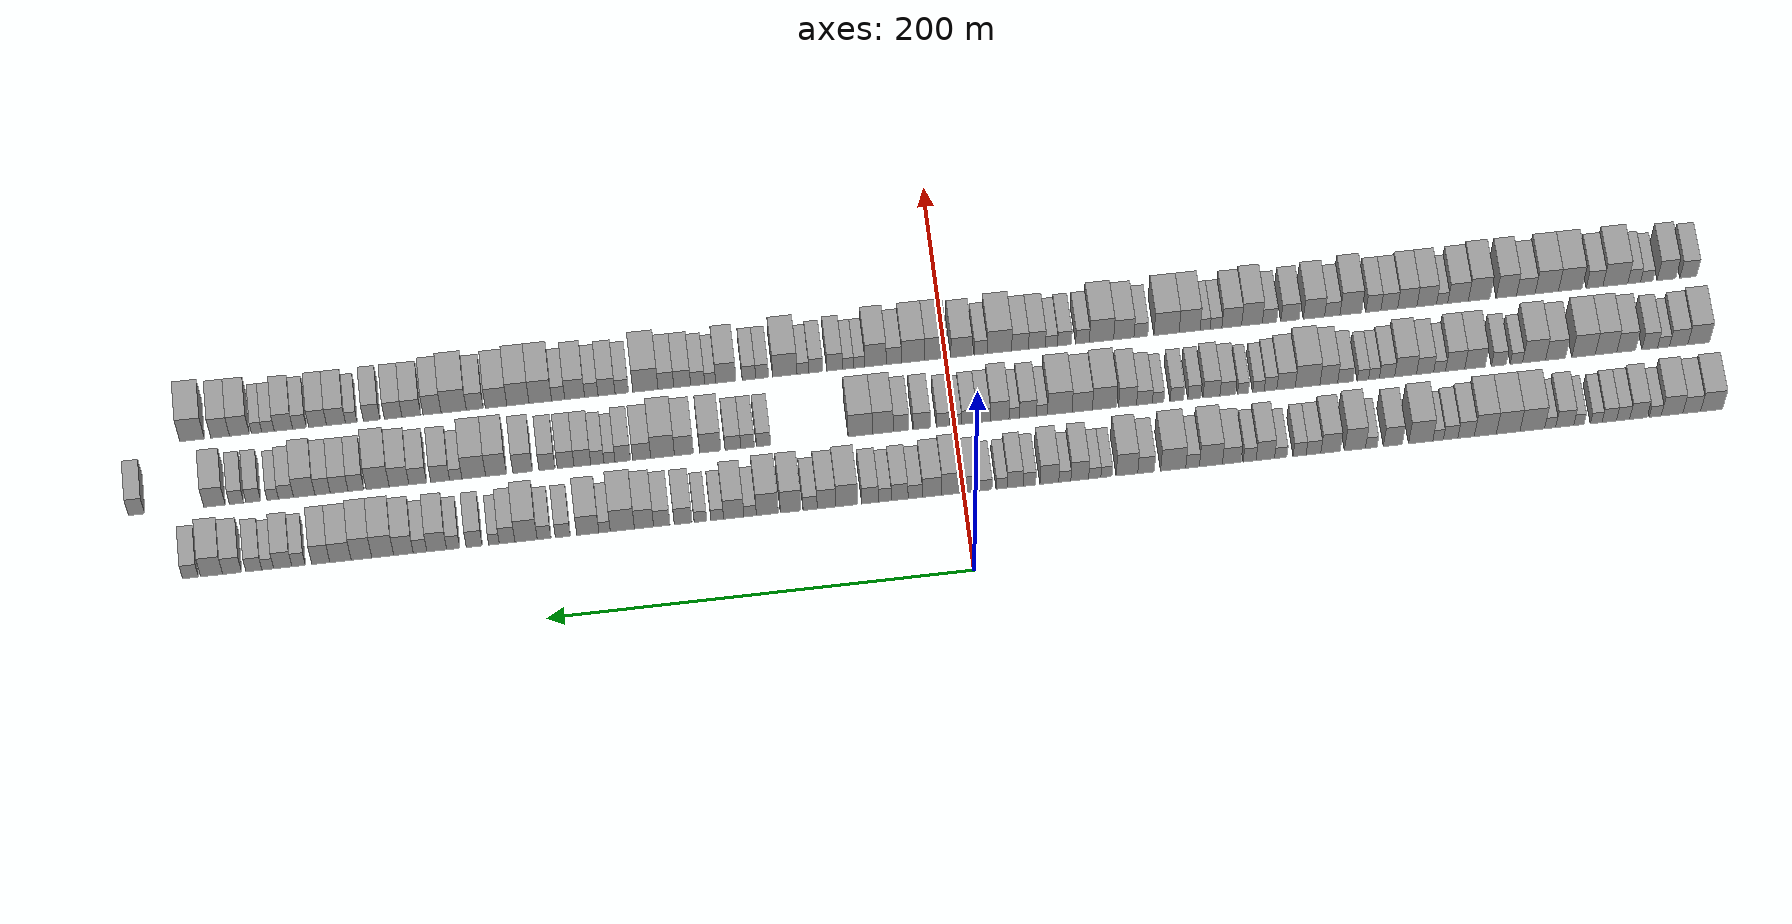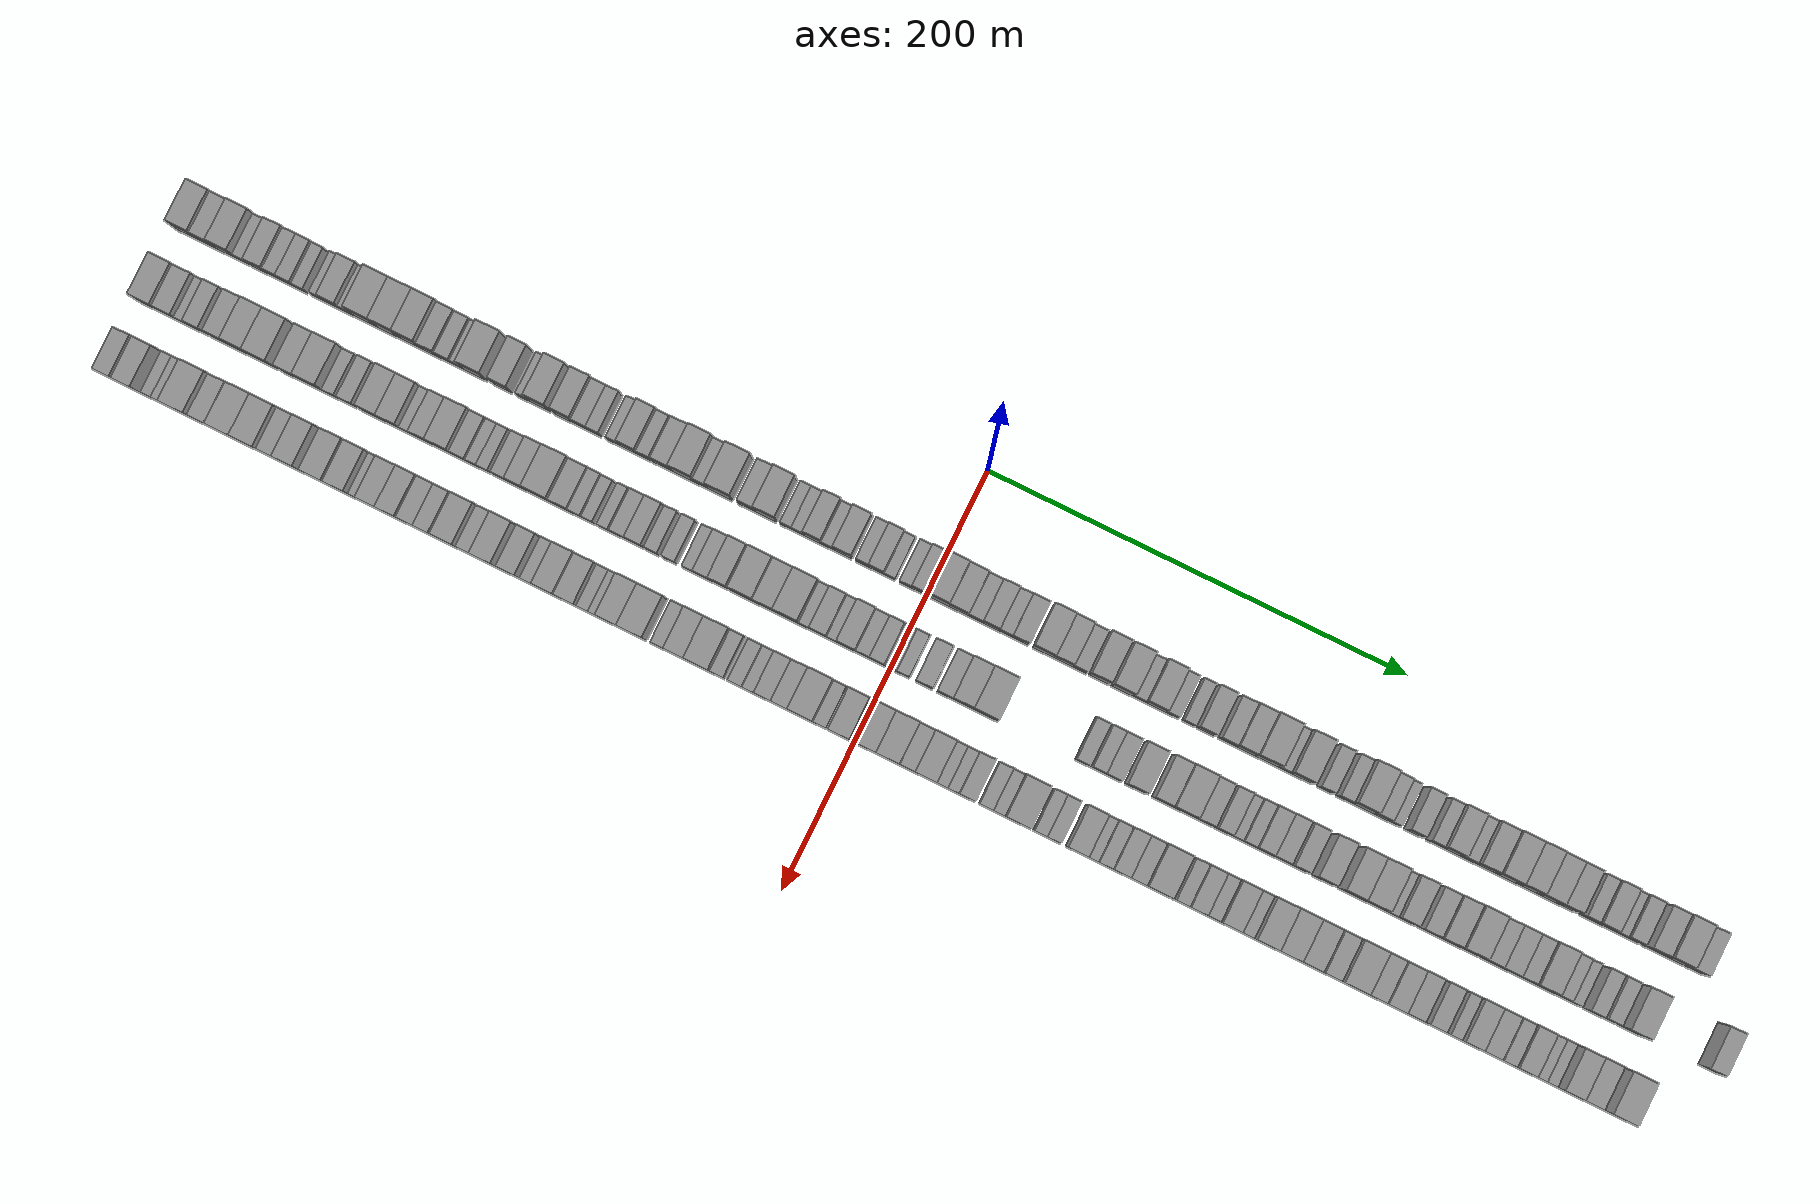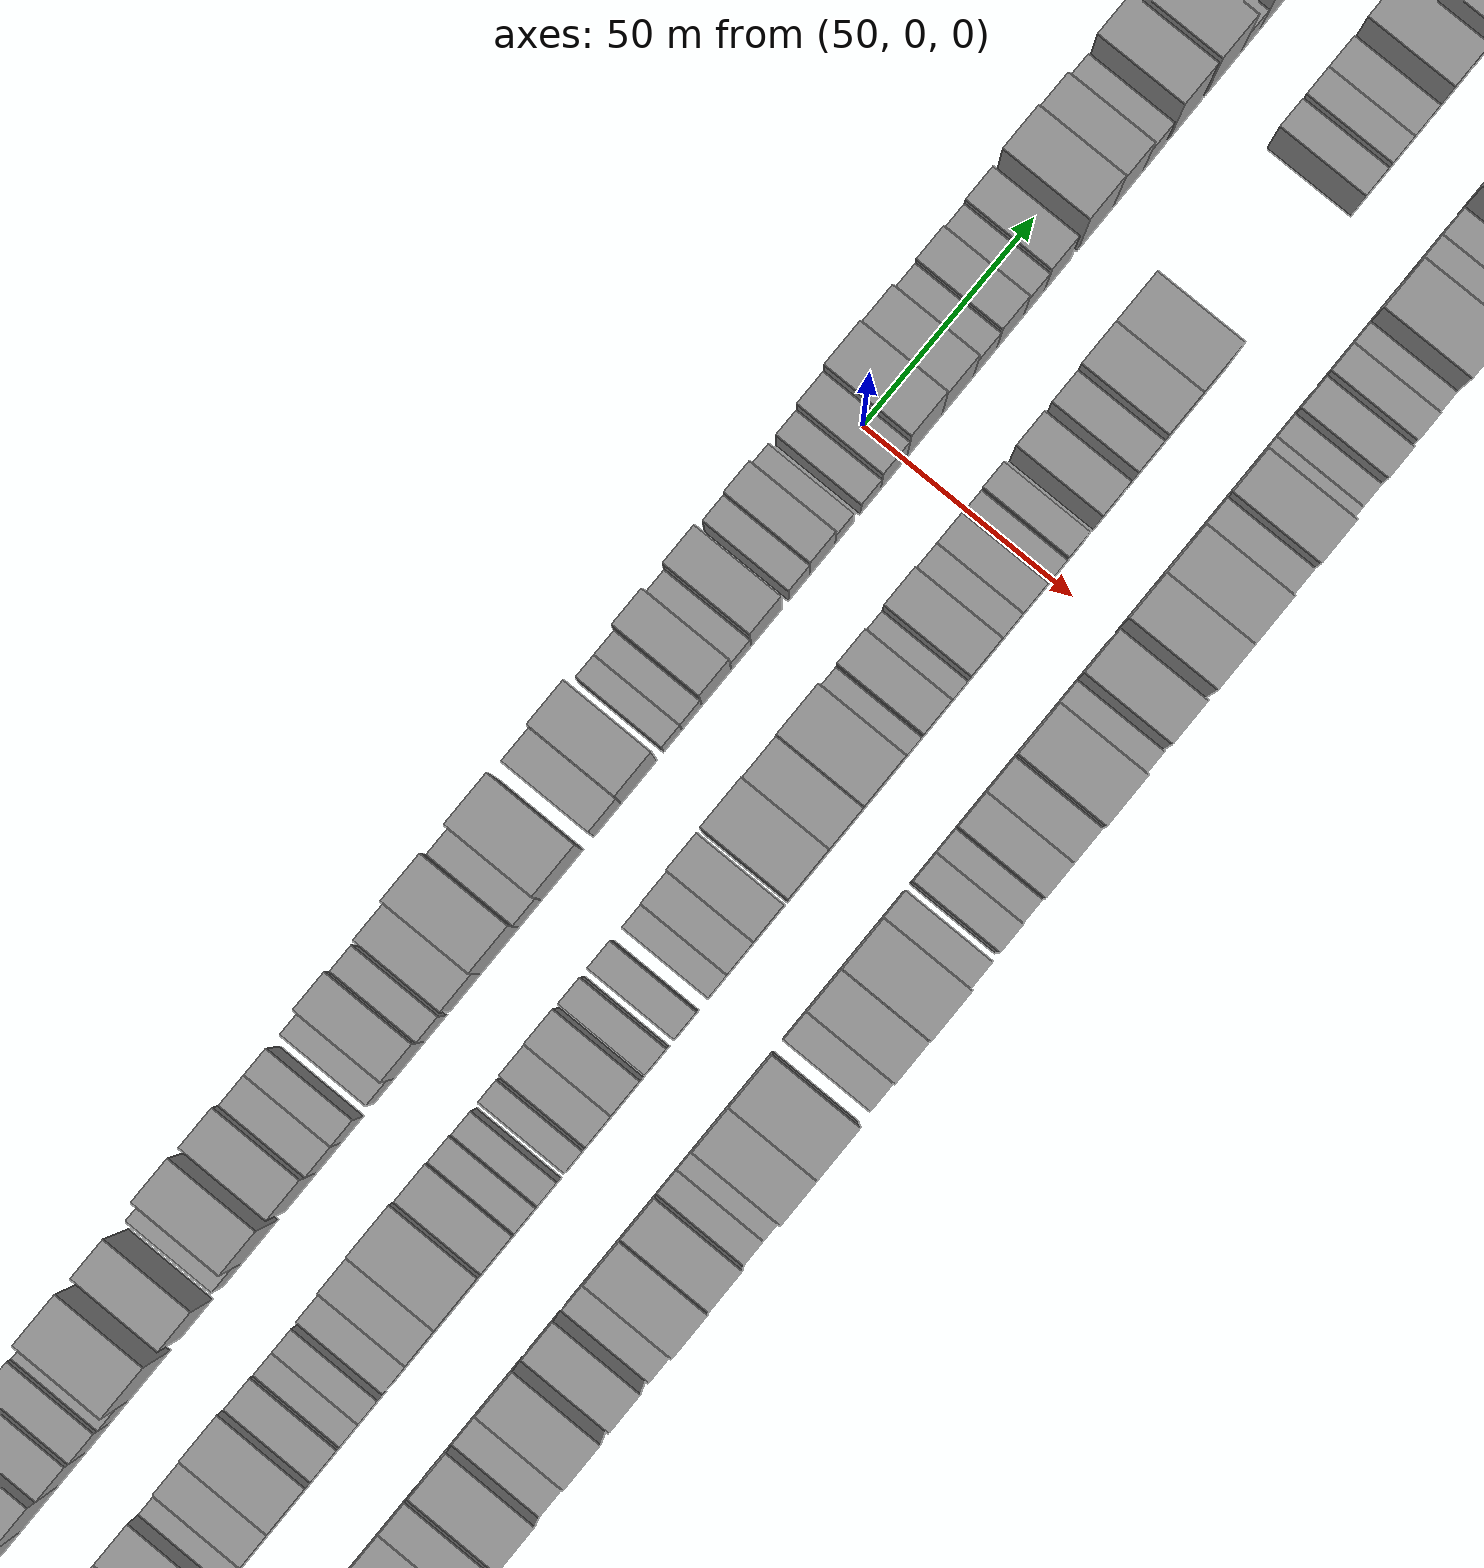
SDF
<sdf version="1.6">
 <world name="default">
  <scene>
   <sky><clouds><speed>12</speed></clouds></sky>
   <ambient>0.4 0.4 0.4 1</ambient>
   <background>0.7 0.7 0.7 1</background>
   <shadows>1</shadows>
  </scene>
  <gravity>0 0 -9.8066</gravity>
  <magnetic_field>6e-06 2.3e-05 -4.2e-05</magnetic_field>
  <physics default="0" name="default_physics" type="ode">
   <ode>
    <solver>
     <type>quick</type>
     <iters>10</iters>
     <sor>1.0</sor>
     <use_dynamic_moi_rescaling>0</use_dynamic_moi_rescaling>
    </solver>
    <constraints>
     <cfm>0</cfm>
     <erp>0.2</erp>
     <contact_max_correcting_vel>100</contact_max_correcting_vel>
     <contact_surface_layer>0.001</contact_surface_layer>
    </constraints>
   </ode>
   <max_step_size>0.004</max_step_size>
   <real_time_factor>1</real_time_factor>
   <real_time_update_rate>250</real_time_update_rate>
  </physics>
  <light name="sun" type="directional">
   <pose>0 0 10 0 0 0</pose>
   <diffuse>0.8 0.8 0.8 1</diffuse>
   <specular>0.2 0.2 0.2 1</specular>
   <attenuation>
    <range>1000</range>
    <constant>0.9</constant>
    <linear>0.01</linear>
    <quadratic>0.001</quadratic>
   </attenuation>
   <direction>-0.5 0.1 -0.9</direction>
  </light>
  <model name="building_1">
   <static>1</static>
   <pose>50.0000 -354.7508 0 0.000000 0.000000 0.000000</pose>
   <link name="link">
    <pose>0 0 10.50 0 0 0</pose>
    <collision name="collision"><geometry><box><size>20.0000 10.4985 21.0000</size></box></geometry></collision>
    <visual name="visual">
     <cast_shadows>0</cast_shadows>
     <geometry><box><size>20.0000 10.4985 21.0000</size></box></geometry>
     <material>
      <script>
       <uri>model://grey_wall/materials/scripts</uri>
       <uri>model://grey_wall/materials/textures</uri>
       <name>vrc/grey_wall</name>
      </script>
     </material>
    </visual>
   </link>
  </model>
  <model name="building_2">
   <static>1</static>
   <pose>50.0000 -345.2587 0 0.000000 0.000000 0.000000</pose>
   <link name="link">
    <pose>0 0 9.00 0 0 0</pose>
    <collision name="collision"><geometry><box><size>20.0000 8.4857 18.0000</size></box></geometry></collision>
    <visual name="visual">
     <cast_shadows>0</cast_shadows>
     <geometry><box><size>20.0000 8.4857 18.0000</size></box></geometry>
     <material>
      <script>
       <uri>model://grey_wall/materials/scripts</uri>
       <uri>model://grey_wall/materials/textures</uri>
       <name>vrc/grey_wall</name>
      </script>
     </material>
    </visual>
   </link>
  </model>
  <model name="building_3">
   <static>1</static>
   <pose>50.0000 -335.8647 0 0.000000 0.000000 0.000000</pose>
   <link name="link">
    <pose>0 0 10.50 0 0 0</pose>
    <collision name="collision"><geometry><box><size>20.0000 10.3022 21.0000</size></box></geometry></collision>
    <visual name="visual">
     <cast_shadows>0</cast_shadows>
     <geometry><box><size>20.0000 10.3022 21.0000</size></box></geometry>
     <material>
      <script>
       <uri>model://grey_wall/materials/scripts</uri>
       <uri>model://grey_wall/materials/textures</uri>
       <name>vrc/grey_wall</name>
      </script>
     </material>
    </visual>
   </link>
  </model>
  <model name="building_4">
   <static>1</static>
   <pose>50.0000 -327.8538 0 0.000000 0.000000 0.000000</pose>
   <link name="link">
    <pose>0 0 6.00 0 0 0</pose>
    <collision name="collision"><geometry><box><size>20.0000 5.7197 12.0000</size></box></geometry></collision>
    <visual name="visual">
     <cast_shadows>0</cast_shadows>
     <geometry><box><size>20.0000 5.7197 12.0000</size></box></geometry>
     <material>
      <script>
       <uri>model://grey_wall/materials/scripts</uri>
       <uri>model://grey_wall/materials/textures</uri>
       <name>vrc/grey_wall</name>
      </script>
     </material>
    </visual>
   </link>
  </model>
  <model name="building_5">
   <static>1</static>
   <pose>50.0000 -319.8060 0 0.000000 0.000000 0.000000</pose>
   <link name="link">
    <pose>0 0 9.00 0 0 0</pose>
    <collision name="collision"><geometry><box><size>20.0000 8.3759 18.0000</size></box></geometry></collision>
    <visual name="visual">
     <cast_shadows>0</cast_shadows>
     <geometry><box><size>20.0000 8.3759 18.0000</size></box></geometry>
     <material>
      <script>
       <uri>model://grey_wall/materials/scripts</uri>
       <uri>model://grey_wall/materials/textures</uri>
       <name>vrc/grey_wall</name>
      </script>
     </material>
    </visual>
   </link>
  </model>
  <model name="building_6">
   <static>1</static>
   <pose>50.0000 -312.4625 0 0.000000 0.000000 0.000000</pose>
   <link name="link">
    <pose>0 0 7.50 0 0 0</pose>
    <collision name="collision"><geometry><box><size>20.0000 6.3111 15.0000</size></box></geometry></collision>
    <visual name="visual">
     <cast_shadows>0</cast_shadows>
     <geometry><box><size>20.0000 6.3111 15.0000</size></box></geometry>
     <material>
      <script>
       <uri>model://grey_wall/materials/scripts</uri>
       <uri>model://grey_wall/materials/textures</uri>
       <name>vrc/grey_wall</name>
      </script>
     </material>
    </visual>
   </link>
  </model>
  <model name="building_7">
   <static>1</static>
   <pose>50.0000 -305.9101 0 0.000000 0.000000 0.000000</pose>
   <link name="link">
    <pose>0 0 7.50 0 0 0</pose>
    <collision name="collision"><geometry><box><size>20.0000 6.7937 15.0000</size></box></geometry></collision>
    <visual name="visual">
     <cast_shadows>0</cast_shadows>
     <geometry><box><size>20.0000 6.7937 15.0000</size></box></geometry>
     <material>
      <script>
       <uri>model://grey_wall/materials/scripts</uri>
       <uri>model://grey_wall/materials/textures</uri>
       <name>vrc/grey_wall</name>
      </script>
     </material>
    </visual>
   </link>
  </model>
  <model name="building_8">
   <static>1</static>
   <pose>50.0000 -299.7185 0 0.000000 0.000000 0.000000</pose>
   <link name="link">
    <pose>0 0 6.00 0 0 0</pose>
    <collision name="collision"><geometry><box><size>20.0000 5.5895 12.0000</size></box></geometry></collision>
    <visual name="visual">
     <cast_shadows>0</cast_shadows>
     <geometry><box><size>20.0000 5.5895 12.0000</size></box></geometry>
     <material>
      <script>
       <uri>model://grey_wall/materials/scripts</uri>
       <uri>model://grey_wall/materials/textures</uri>
       <name>vrc/grey_wall</name>
      </script>
     </material>
    </visual>
   </link>
  </model>
  <model name="building_9">
   <static>1</static>
   <pose>50.0000 -291.4428 0 0.000000 0.000000 0.000000</pose>
   <link name="link">
    <pose>0 0 6.00 0 0 0</pose>
    <collision name="collision"><geometry><box><size>20.0000 4.9619 12.0000</size></box></geometry></collision>
    <visual name="visual">
     <cast_shadows>0</cast_shadows>
     <geometry><box><size>20.0000 4.9619 12.0000</size></box></geometry>
     <material>
      <script>
       <uri>model://grey_wall/materials/scripts</uri>
       <uri>model://grey_wall/materials/textures</uri>
       <name>vrc/grey_wall</name>
      </script>
     </material>
    </visual>
   </link>
  </model>
  <model name="building_10">
   <static>1</static>
   <pose>50.0000 -284.6421 0 0.000000 0.000000 0.000000</pose>
   <link name="link">
    <pose>0 0 9.00 0 0 0</pose>
    <collision name="collision"><geometry><box><size>20.0000 8.6395 18.0000</size></box></geometry></collision>
    <visual name="visual">
     <cast_shadows>0</cast_shadows>
     <geometry><box><size>20.0000 8.6395 18.0000</size></box></geometry>
     <material>
      <script>
       <uri>model://grey_wall/materials/scripts</uri>
       <uri>model://grey_wall/materials/textures</uri>
       <name>vrc/grey_wall</name>
      </script>
     </material>
    </visual>
   </link>
  </model>
  <model name="building_11">
   <static>1</static>
   <pose>50.0000 -277.6937 0 0.000000 0.000000 0.000000</pose>
   <link name="link">
    <pose>0 0 6.00 0 0 0</pose>
    <collision name="collision"><geometry><box><size>20.0000 5.2573 12.0000</size></box></geometry></collision>
    <visual name="visual">
     <cast_shadows>0</cast_shadows>
     <geometry><box><size>20.0000 5.2573 12.0000</size></box></geometry>
     <material>
      <script>
       <uri>model://grey_wall/materials/scripts</uri>
       <uri>model://grey_wall/materials/textures</uri>
       <name>vrc/grey_wall</name>
      </script>
     </material>
    </visual>
   </link>
  </model>
  <model name="building_12">
   <static>1</static>
   <pose>50.0000 -269.2104 0 0.000000 0.000000 0.000000</pose>
   <link name="link">
    <pose>0 0 12.00 0 0 0</pose>
    <collision name="collision"><geometry><box><size>20.0000 11.7094 24.0000</size></box></geometry></collision>
    <visual name="visual">
     <cast_shadows>0</cast_shadows>
     <geometry><box><size>20.0000 11.7094 24.0000</size></box></geometry>
     <material>
      <script>
       <uri>model://grey_wall/materials/scripts</uri>
       <uri>model://grey_wall/materials/textures</uri>
       <name>vrc/grey_wall</name>
      </script>
     </material>
    </visual>
   </link>
  </model>
  <model name="building_13">
   <static>1</static>
   <pose>50.0000 -257.7346 0 0.000000 0.000000 0.000000</pose>
   <link name="link">
    <pose>0 0 12.00 0 0 0</pose>
    <collision name="collision"><geometry><box><size>20.0000 11.2421 24.0000</size></box></geometry></collision>
    <visual name="visual">
     <cast_shadows>0</cast_shadows>
     <geometry><box><size>20.0000 11.2421 24.0000</size></box></geometry>
     <material>
      <script>
       <uri>model://grey_wall/materials/scripts</uri>
       <uri>model://grey_wall/materials/textures</uri>
       <name>vrc/grey_wall</name>
      </script>
     </material>
    </visual>
   </link>
  </model>
  <model name="building_14">
   <static>1</static>
   <pose>50.0000 -246.8696 0 0.000000 0.000000 0.000000</pose>
   <link name="link">
    <pose>0 0 12.00 0 0 0</pose>
    <collision name="collision"><geometry><box><size>20.0000 10.4880 24.0000</size></box></geometry></collision>
    <visual name="visual">
     <cast_shadows>0</cast_shadows>
     <geometry><box><size>20.0000 10.4880 24.0000</size></box></geometry>
     <material>
      <script>
       <uri>model://grey_wall/materials/scripts</uri>
       <uri>model://grey_wall/materials/textures</uri>
       <name>vrc/grey_wall</name>
      </script>
     </material>
    </visual>
   </link>
  </model>
  <model name="building_15">
   <static>1</static>
   <pose>50.0000 -237.7019 0 0.000000 0.000000 0.000000</pose>
   <link name="link">
    <pose>0 0 9.00 0 0 0</pose>
    <collision name="collision"><geometry><box><size>20.0000 7.8472 18.0000</size></box></geometry></collision>
    <visual name="visual">
     <cast_shadows>0</cast_shadows>
     <geometry><box><size>20.0000 7.8472 18.0000</size></box></geometry>
     <material>
      <script>
       <uri>model://grey_wall/materials/scripts</uri>
       <uri>model://grey_wall/materials/textures</uri>
       <name>vrc/grey_wall</name>
      </script>
     </material>
    </visual>
   </link>
  </model>
  <model name="building_16">
   <static>1</static>
   <pose>50.0000 -230.3300 0 0.000000 0.000000 0.000000</pose>
   <link name="link">
    <pose>0 0 7.50 0 0 0</pose>
    <collision name="collision"><geometry><box><size>20.0000 6.8967 15.0000</size></box></geometry></collision>
    <visual name="visual">
     <cast_shadows>0</cast_shadows>
     <geometry><box><size>20.0000 6.8967 15.0000</size></box></geometry>
     <material>
      <script>
       <uri>model://grey_wall/materials/scripts</uri>
       <uri>model://grey_wall/materials/textures</uri>
       <name>vrc/grey_wall</name>
      </script>
     </material>
    </visual>
   </link>
  </model>
  <model name="building_17">
   <static>1</static>
   <pose>50.0000 -224.3962 0 0.000000 0.000000 0.000000</pose>
   <link name="link">
    <pose>0 0 6.00 0 0 0</pose>
    <collision name="collision"><geometry><box><size>20.0000 4.9710 12.0000</size></box></geometry></collision>
    <visual name="visual">
     <cast_shadows>0</cast_shadows>
     <geometry><box><size>20.0000 4.9710 12.0000</size></box></geometry>
     <material>
      <script>
       <uri>model://grey_wall/materials/scripts</uri>
       <uri>model://grey_wall/materials/textures</uri>
       <name>vrc/grey_wall</name>
      </script>
     </material>
    </visual>
   </link>
  </model>
  <model name="building_18">
   <static>1</static>
   <pose>50.0000 -216.1369 0 0.000000 0.000000 0.000000</pose>
   <link name="link">
    <pose>0 0 12.00 0 0 0</pose>
    <collision name="collision"><geometry><box><size>20.0000 11.5476 24.0000</size></box></geometry></collision>
    <visual name="visual">
     <cast_shadows>0</cast_shadows>
     <geometry><box><size>20.0000 11.5476 24.0000</size></box></geometry>
     <material>
      <script>
       <uri>model://grey_wall/materials/scripts</uri>
       <uri>model://grey_wall/materials/textures</uri>
       <name>vrc/grey_wall</name>
      </script>
     </material>
    </visual>
   </link>
  </model>
  <model name="building_19">
   <static>1</static>
   <pose>50.0000 -202.8741 0 0.000000 0.000000 0.000000</pose>
   <link name="link">
    <pose>0 0 10.50 0 0 0</pose>
    <collision name="collision"><geometry><box><size>20.0000 8.9781 21.0000</size></box></geometry></collision>
    <visual name="visual">
     <cast_shadows>0</cast_shadows>
     <geometry><box><size>20.0000 8.9781 21.0000</size></box></geometry>
     <material>
      <script>
       <uri>model://grey_wall/materials/scripts</uri>
       <uri>model://grey_wall/materials/textures</uri>
       <name>vrc/grey_wall</name>
      </script>
     </material>
    </visual>
   </link>
  </model>
  <model name="building_20">
   <static>1</static>
   <pose>50.0000 -192.6304 0 0.000000 0.000000 0.000000</pose>
   <link name="link">
    <pose>0 0 6.00 0 0 0</pose>
    <collision name="collision"><geometry><box><size>20.0000 5.5092 12.0000</size></box></geometry></collision>
    <visual name="visual">
     <cast_shadows>0</cast_shadows>
     <geometry><box><size>20.0000 5.5092 12.0000</size></box></geometry>
     <material>
      <script>
       <uri>model://grey_wall/materials/scripts</uri>
       <uri>model://grey_wall/materials/textures</uri>
       <name>vrc/grey_wall</name>
      </script>
     </material>
    </visual>
   </link>
  </model>
  <model name="building_21">
   <static>1</static>
   <pose>50.0000 -184.8800 0 0.000000 0.000000 0.000000</pose>
   <link name="link">
    <pose>0 0 12.00 0 0 0</pose>
    <collision name="collision"><geometry><box><size>20.0000 9.9916 24.0000</size></box></geometry></collision>
    <visual name="visual">
     <cast_shadows>0</cast_shadows>
     <geometry><box><size>20.0000 9.9916 24.0000</size></box></geometry>
     <material>
      <script>
       <uri>model://grey_wall/materials/scripts</uri>
       <uri>model://grey_wall/materials/textures</uri>
       <name>vrc/grey_wall</name>
      </script>
     </material>
    </visual>
   </link>
  </model>
  <model name="building_22">
   <static>1</static>
   <pose>50.0000 -173.2821 0 0.000000 0.000000 0.000000</pose>
   <link name="link">
    <pose>0 0 10.50 0 0 0</pose>
    <collision name="collision"><geometry><box><size>20.0000 9.2042 21.0000</size></box></geometry></collision>
    <visual name="visual">
     <cast_shadows>0</cast_shadows>
     <geometry><box><size>20.0000 9.2042 21.0000</size></box></geometry>
     <material>
      <script>
       <uri>model://grey_wall/materials/scripts</uri>
       <uri>model://grey_wall/materials/textures</uri>
       <name>vrc/grey_wall</name>
      </script>
     </material>
    </visual>
   </link>
  </model>
  <model name="building_23">
   <static>1</static>
   <pose>50.0000 -165.1780 0 0.000000 0.000000 0.000000</pose>
   <link name="link">
    <pose>0 0 7.50 0 0 0</pose>
    <collision name="collision"><geometry><box><size>20.0000 7.0040 15.0000</size></box></geometry></collision>
    <visual name="visual">
     <cast_shadows>0</cast_shadows>
     <geometry><box><size>20.0000 7.0040 15.0000</size></box></geometry>
     <material>
      <script>
       <uri>model://grey_wall/materials/scripts</uri>
       <uri>model://grey_wall/materials/textures</uri>
       <name>vrc/grey_wall</name>
      </script>
     </material>
    </visual>
   </link>
  </model>
  <model name="building_24">
   <static>1</static>
   <pose>50.0000 -158.6094 0 0.000000 0.000000 0.000000</pose>
   <link name="link">
    <pose>0 0 7.50 0 0 0</pose>
    <collision name="collision"><geometry><box><size>20.0000 6.1332 15.0000</size></box></geometry></collision>
    <visual name="visual">
     <cast_shadows>0</cast_shadows>
     <geometry><box><size>20.0000 6.1332 15.0000</size></box></geometry>
     <material>
      <script>
       <uri>model://grey_wall/materials/scripts</uri>
       <uri>model://grey_wall/materials/textures</uri>
       <name>vrc/grey_wall</name>
      </script>
     </material>
    </visual>
   </link>
  </model>
  <model name="building_25">
   <static>1</static>
   <pose>50.0000 -149.6114 0 0.000000 0.000000 0.000000</pose>
   <link name="link">
    <pose>0 0 6.00 0 0 0</pose>
    <collision name="collision"><geometry><box><size>20.0000 5.8628 12.0000</size></box></geometry></collision>
    <visual name="visual">
     <cast_shadows>0</cast_shadows>
     <geometry><box><size>20.0000 5.8628 12.0000</size></box></geometry>
     <material>
      <script>
       <uri>model://grey_wall/materials/scripts</uri>
       <uri>model://grey_wall/materials/textures</uri>
       <name>vrc/grey_wall</name>
      </script>
     </material>
    </visual>
   </link>
  </model>
  <model name="building_26">
   <static>1</static>
   <pose>50.0000 -142.3079 0 0.000000 0.000000 0.000000</pose>
   <link name="link">
    <pose>0 0 10.50 0 0 0</pose>
    <collision name="collision"><geometry><box><size>20.0000 8.7442 21.0000</size></box></geometry></collision>
    <visual name="visual">
     <cast_shadows>0</cast_shadows>
     <geometry><box><size>20.0000 8.7442 21.0000</size></box></geometry>
     <material>
      <script>
       <uri>model://grey_wall/materials/scripts</uri>
       <uri>model://grey_wall/materials/textures</uri>
       <name>vrc/grey_wall</name>
      </script>
     </material>
    </visual>
   </link>
  </model>
  <model name="building_27">
   <static>1</static>
   <pose>50.0000 -134.8896 0 0.000000 0.000000 0.000000</pose>
   <link name="link">
    <pose>0 0 7.50 0 0 0</pose>
    <collision name="collision"><geometry><box><size>20.0000 6.0924 15.0000</size></box></geometry></collision>
    <visual name="visual">
     <cast_shadows>0</cast_shadows>
     <geometry><box><size>20.0000 6.0924 15.0000</size></box></geometry>
     <material>
      <script>
       <uri>model://grey_wall/materials/scripts</uri>
       <uri>model://grey_wall/materials/textures</uri>
       <name>vrc/grey_wall</name>
      </script>
     </material>
    </visual>
   </link>
  </model>
  <model name="building_28">
   <static>1</static>
   <pose>50.0000 -126.4223 0 0.000000 0.000000 0.000000</pose>
   <link name="link">
    <pose>0 0 9.00 0 0 0</pose>
    <collision name="collision"><geometry><box><size>20.0000 8.8422 18.0000</size></box></geometry></collision>
    <visual name="visual">
     <cast_shadows>0</cast_shadows>
     <geometry><box><size>20.0000 8.8422 18.0000</size></box></geometry>
     <material>
      <script>
       <uri>model://grey_wall/materials/scripts</uri>
       <uri>model://grey_wall/materials/textures</uri>
       <name>vrc/grey_wall</name>
      </script>
     </material>
    </visual>
   </link>
  </model>
  <model name="building_29">
   <static>1</static>
   <pose>50.0000 -116.5494 0 0.000000 0.000000 0.000000</pose>
   <link name="link">
    <pose>0 0 12.00 0 0 0</pose>
    <collision name="collision"><geometry><box><size>20.0000 10.9035 24.0000</size></box></geometry></collision>
    <visual name="visual">
     <cast_shadows>0</cast_shadows>
     <geometry><box><size>20.0000 10.9035 24.0000</size></box></geometry>
     <material>
      <script>
       <uri>model://grey_wall/materials/scripts</uri>
       <uri>model://grey_wall/materials/textures</uri>
       <name>vrc/grey_wall</name>
      </script>
     </material>
    </visual>
   </link>
  </model>
  <model name="building_30">
   <static>1</static>
   <pose>50.0000 -107.8798 0 0.000000 0.000000 0.000000</pose>
   <link name="link">
    <pose>0 0 7.50 0 0 0</pose>
    <collision name="collision"><geometry><box><size>20.0000 6.4356 15.0000</size></box></geometry></collision>
    <visual name="visual">
     <cast_shadows>0</cast_shadows>
     <geometry><box><size>20.0000 6.4356 15.0000</size></box></geometry>
     <material>
      <script>
       <uri>model://grey_wall/materials/scripts</uri>
       <uri>model://grey_wall/materials/textures</uri>
       <name>vrc/grey_wall</name>
      </script>
     </material>
    </visual>
   </link>
  </model>
  <model name="building_31">
   <static>1</static>
   <pose>50.0000 -98.7202 0 0.000000 0.000000 0.000000</pose>
   <link name="link">
    <pose>0 0 12.00 0 0 0</pose>
    <collision name="collision"><geometry><box><size>20.0000 11.8837 24.0000</size></box></geometry></collision>
    <visual name="visual">
     <cast_shadows>0</cast_shadows>
     <geometry><box><size>20.0000 11.8837 24.0000</size></box></geometry>
     <material>
      <script>
       <uri>model://grey_wall/materials/scripts</uri>
       <uri>model://grey_wall/materials/textures</uri>
       <name>vrc/grey_wall</name>
      </script>
     </material>
    </visual>
   </link>
  </model>
  <model name="building_32">
   <static>1</static>
   <pose>50.0000 -85.8692 0 0.000000 0.000000 0.000000</pose>
   <link name="link">
    <pose>0 0 9.00 0 0 0</pose>
    <collision name="collision"><geometry><box><size>20.0000 7.8184 18.0000</size></box></geometry></collision>
    <visual name="visual">
     <cast_shadows>0</cast_shadows>
     <geometry><box><size>20.0000 7.8184 18.0000</size></box></geometry>
     <material>
      <script>
       <uri>model://grey_wall/materials/scripts</uri>
       <uri>model://grey_wall/materials/textures</uri>
       <name>vrc/grey_wall</name>
      </script>
     </material>
    </visual>
   </link>
  </model>
  <model name="building_33">
   <static>1</static>
   <pose>50.0000 -76.8457 0 0.000000 0.000000 0.000000</pose>
   <link name="link">
    <pose>0 0 12.00 0 0 0</pose>
    <collision name="collision"><geometry><box><size>20.0000 10.2286 24.0000</size></box></geometry></collision>
    <visual name="visual">
     <cast_shadows>0</cast_shadows>
     <geometry><box><size>20.0000 10.2286 24.0000</size></box></geometry>
     <material>
      <script>
       <uri>model://grey_wall/materials/scripts</uri>
       <uri>model://grey_wall/materials/textures</uri>
       <name>vrc/grey_wall</name>
      </script>
     </material>
    </visual>
   </link>
  </model>
  <model name="building_34">
   <static>1</static>
   <pose>50.0000 -67.1187 0 0.000000 0.000000 0.000000</pose>
   <link name="link">
    <pose>0 0 6.00 0 0 0</pose>
    <collision name="collision"><geometry><box><size>20.0000 5.2254 12.0000</size></box></geometry></collision>
    <visual name="visual">
     <cast_shadows>0</cast_shadows>
     <geometry><box><size>20.0000 5.2254 12.0000</size></box></geometry>
     <material>
      <script>
       <uri>model://grey_wall/materials/scripts</uri>
       <uri>model://grey_wall/materials/textures</uri>
       <name>vrc/grey_wall</name>
      </script>
     </material>
    </visual>
   </link>
  </model>
  <model name="building_35">
   <static>1</static>
   <pose>50.0000 -61.6264 0 0.000000 0.000000 0.000000</pose>
   <link name="link">
    <pose>0 0 6.00 0 0 0</pose>
    <collision name="collision"><geometry><box><size>20.0000 5.7592 12.0000</size></box></geometry></collision>
    <visual name="visual">
     <cast_shadows>0</cast_shadows>
     <geometry><box><size>20.0000 5.7592 12.0000</size></box></geometry>
     <material>
      <script>
       <uri>model://grey_wall/materials/scripts</uri>
       <uri>model://grey_wall/materials/textures</uri>
       <name>vrc/grey_wall</name>
      </script>
     </material>
    </visual>
   </link>
  </model>
  <model name="building_36">
   <static>1</static>
   <pose>50.0000 -54.5403 0 0.000000 0.000000 0.000000</pose>
   <link name="link">
    <pose>0 0 10.50 0 0 0</pose>
    <collision name="collision"><geometry><box><size>20.0000 8.4130 21.0000</size></box></geometry></collision>
    <visual name="visual">
     <cast_shadows>0</cast_shadows>
     <geometry><box><size>20.0000 8.4130 21.0000</size></box></geometry>
     <material>
      <script>
       <uri>model://grey_wall/materials/scripts</uri>
       <uri>model://grey_wall/materials/textures</uri>
       <name>vrc/grey_wall</name>
      </script>
     </material>
    </visual>
   </link>
  </model>
  <model name="building_37">
   <static>1</static>
   <pose>50.0000 -47.4788 0 0.000000 0.000000 0.000000</pose>
   <link name="link">
    <pose>0 0 6.00 0 0 0</pose>
    <collision name="collision"><geometry><box><size>20.0000 5.7098 12.0000</size></box></geometry></collision>
    <visual name="visual">
     <cast_shadows>0</cast_shadows>
     <geometry><box><size>20.0000 5.7098 12.0000</size></box></geometry>
     <material>
      <script>
       <uri>model://grey_wall/materials/scripts</uri>
       <uri>model://grey_wall/materials/textures</uri>
       <name>vrc/grey_wall</name>
      </script>
     </material>
    </visual>
   </link>
  </model>
  <model name="building_38">
   <static>1</static>
   <pose>50.0000 -40.1824 0 0.000000 0.000000 0.000000</pose>
   <link name="link">
    <pose>0 0 10.50 0 0 0</pose>
    <collision name="collision"><geometry><box><size>20.0000 8.8831 21.0000</size></box></geometry></collision>
    <visual name="visual">
     <cast_shadows>0</cast_shadows>
     <geometry><box><size>20.0000 8.8831 21.0000</size></box></geometry>
     <material>
      <script>
       <uri>model://grey_wall/materials/scripts</uri>
       <uri>model://grey_wall/materials/textures</uri>
       <name>vrc/grey_wall</name>
      </script>
     </material>
    </visual>
   </link>
  </model>
  <model name="building_39">
   <static>1</static>
   <pose>50.0000 -30.7308 0 0.000000 0.000000 0.000000</pose>
   <link name="link">
    <pose>0 0 7.50 0 0 0</pose>
    <collision name="collision"><geometry><box><size>20.0000 6.0201 15.0000</size></box></geometry></collision>
    <visual name="visual">
     <cast_shadows>0</cast_shadows>
     <geometry><box><size>20.0000 6.0201 15.0000</size></box></geometry>
     <material>
      <script>
       <uri>model://grey_wall/materials/scripts</uri>
       <uri>model://grey_wall/materials/textures</uri>
       <name>vrc/grey_wall</name>
      </script>
     </material>
    </visual>
   </link>
  </model>
  <model name="building_40">
   <static>1</static>
   <pose>50.0000 -24.0567 0 0.000000 0.000000 0.000000</pose>
   <link name="link">
    <pose>0 0 9.00 0 0 0</pose>
    <collision name="collision"><geometry><box><size>20.0000 7.3281 18.0000</size></box></geometry></collision>
    <visual name="visual">
     <cast_shadows>0</cast_shadows>
     <geometry><box><size>20.0000 7.3281 18.0000</size></box></geometry>
     <material>
      <script>
       <uri>model://grey_wall/materials/scripts</uri>
       <uri>model://grey_wall/materials/textures</uri>
       <name>vrc/grey_wall</name>
      </script>
     </material>
    </visual>
   </link>
  </model>
  <model name="building_41">
   <static>1</static>
   <pose>50.0000 -17.7260 0 0.000000 0.000000 0.000000</pose>
   <link name="link">
    <pose>0 0 6.00 0 0 0</pose>
    <collision name="collision"><geometry><box><size>20.0000 5.3332 12.0000</size></box></geometry></collision>
    <visual name="visual">
     <cast_shadows>0</cast_shadows>
     <geometry><box><size>20.0000 5.3332 12.0000</size></box></geometry>
     <material>
      <script>
       <uri>model://grey_wall/materials/scripts</uri>
       <uri>model://grey_wall/materials/textures</uri>
       <name>vrc/grey_wall</name>
      </script>
     </material>
    </visual>
   </link>
  </model>
  <model name="building_42">
   <static>1</static>
   <pose>50.0000 -10.1235 0 0.000000 0.000000 0.000000</pose>
   <link name="link">
    <pose>0 0 6.00 0 0 0</pose>
    <collision name="collision"><geometry><box><size>20.0000 5.8719 12.0000</size></box></geometry></collision>
    <visual name="visual">
     <cast_shadows>0</cast_shadows>
     <geometry><box><size>20.0000 5.8719 12.0000</size></box></geometry>
     <material>
      <script>
       <uri>model://grey_wall/materials/scripts</uri>
       <uri>model://grey_wall/materials/textures</uri>
       <name>vrc/grey_wall</name>
      </script>
     </material>
    </visual>
   </link>
  </model>
  <model name="building_43">
   <static>1</static>
   <pose>50.0000 -3.4062 0 0.000000 0.000000 0.000000</pose>
   <link name="link">
    <pose>0 0 9.00 0 0 0</pose>
    <collision name="collision"><geometry><box><size>20.0000 7.5627 18.0000</size></box></geometry></collision>
    <visual name="visual">
     <cast_shadows>0</cast_shadows>
     <geometry><box><size>20.0000 7.5627 18.0000</size></box></geometry>
     <material>
      <script>
       <uri>model://grey_wall/materials/scripts</uri>
       <uri>model://grey_wall/materials/textures</uri>
       <name>vrc/grey_wall</name>
      </script>
     </material>
    </visual>
   </link>
  </model>
  <model name="building_44">
   <static>1</static>
   <pose>50.0000 5.4814 0 0.000000 0.000000 0.000000</pose>
   <link name="link">
    <pose>0 0 12.00 0 0 0</pose>
    <collision name="collision"><geometry><box><size>20.0000 10.2124 24.0000</size></box></geometry></collision>
    <visual name="visual">
     <cast_shadows>0</cast_shadows>
     <geometry><box><size>20.0000 10.2124 24.0000</size></box></geometry>
     <material>
      <script>
       <uri>model://grey_wall/materials/scripts</uri>
       <uri>model://grey_wall/materials/textures</uri>
       <name>vrc/grey_wall</name>
      </script>
     </material>
    </visual>
   </link>
  </model>
  <model name="building_45">
   <static>1</static>
   <pose>50.0000 15.1778 0 0.000000 0.000000 0.000000</pose>
   <link name="link">
    <pose>0 0 10.50 0 0 0</pose>
    <collision name="collision"><geometry><box><size>20.0000 9.1802 21.0000</size></box></geometry></collision>
    <visual name="visual">
     <cast_shadows>0</cast_shadows>
     <geometry><box><size>20.0000 9.1802 21.0000</size></box></geometry>
     <material>
      <script>
       <uri>model://grey_wall/materials/scripts</uri>
       <uri>model://grey_wall/materials/textures</uri>
       <name>vrc/grey_wall</name>
      </script>
     </material>
    </visual>
   </link>
  </model>
  <model name="building_46">
   <static>1</static>
   <pose>50.0000 23.1349 0 0.000000 0.000000 0.000000</pose>
   <link name="link">
    <pose>0 0 7.50 0 0 0</pose>
    <collision name="collision"><geometry><box><size>20.0000 6.7341 15.0000</size></box></geometry></collision>
    <visual name="visual">
     <cast_shadows>0</cast_shadows>
     <geometry><box><size>20.0000 6.7341 15.0000</size></box></geometry>
     <material>
      <script>
       <uri>model://grey_wall/materials/scripts</uri>
       <uri>model://grey_wall/materials/textures</uri>
       <name>vrc/grey_wall</name>
      </script>
     </material>
    </visual>
   </link>
  </model>
  <model name="building_47">
   <static>1</static>
   <pose>50.0000 30.4223 0 0.000000 0.000000 0.000000</pose>
   <link name="link">
    <pose>0 0 9.00 0 0 0</pose>
    <collision name="collision"><geometry><box><size>20.0000 7.8408 18.0000</size></box></geometry></collision>
    <visual name="visual">
     <cast_shadows>0</cast_shadows>
     <geometry><box><size>20.0000 7.8408 18.0000</size></box></geometry>
     <material>
      <script>
       <uri>model://grey_wall/materials/scripts</uri>
       <uri>model://grey_wall/materials/textures</uri>
       <name>vrc/grey_wall</name>
      </script>
     </material>
    </visual>
   </link>
  </model>
  <model name="building_48">
   <static>1</static>
   <pose>50.0000 37.3837 0 0.000000 0.000000 0.000000</pose>
   <link name="link">
    <pose>0 0 7.50 0 0 0</pose>
    <collision name="collision"><geometry><box><size>20.0000 6.0819 15.0000</size></box></geometry></collision>
    <visual name="visual">
     <cast_shadows>0</cast_shadows>
     <geometry><box><size>20.0000 6.0819 15.0000</size></box></geometry>
     <material>
      <script>
       <uri>model://grey_wall/materials/scripts</uri>
       <uri>model://grey_wall/materials/textures</uri>
       <name>vrc/grey_wall</name>
      </script>
     </material>
    </visual>
   </link>
  </model>
  <model name="building_49">
   <static>1</static>
   <pose>50.0000 44.3541 0 0.000000 0.000000 0.000000</pose>
   <link name="link">
    <pose>0 0 9.00 0 0 0</pose>
    <collision name="collision"><geometry><box><size>20.0000 7.8590 18.0000</size></box></geometry></collision>
    <visual name="visual">
     <cast_shadows>0</cast_shadows>
     <geometry><box><size>20.0000 7.8590 18.0000</size></box></geometry>
     <material>
      <script>
       <uri>model://grey_wall/materials/scripts</uri>
       <uri>model://grey_wall/materials/textures</uri>
       <name>vrc/grey_wall</name>
      </script>
     </material>
    </visual>
   </link>
  </model>
  <model name="building_50">
   <static>1</static>
   <pose>50.0000 55.3763 0 0.000000 0.000000 0.000000</pose>
   <link name="link">
    <pose>0 0 12.00 0 0 0</pose>
    <collision name="collision"><geometry><box><size>20.0000 10.1853 24.0000</size></box></geometry></collision>
    <visual name="visual">
     <cast_shadows>0</cast_shadows>
     <geometry><box><size>20.0000 10.1853 24.0000</size></box></geometry>
     <material>
      <script>
       <uri>model://grey_wall/materials/scripts</uri>
       <uri>model://grey_wall/materials/textures</uri>
       <name>vrc/grey_wall</name>
      </script>
     </material>
    </visual>
   </link>
  </model>
  <model name="building_51">
   <static>1</static>
   <pose>50.0000 64.8415 0 0.000000 0.000000 0.000000</pose>
   <link name="link">
    <pose>0 0 10.50 0 0 0</pose>
    <collision name="collision"><geometry><box><size>20.0000 8.7452 21.0000</size></box></geometry></collision>
    <visual name="visual">
     <cast_shadows>0</cast_shadows>
     <geometry><box><size>20.0000 8.7452 21.0000</size></box></geometry>
     <material>
      <script>
       <uri>model://grey_wall/materials/scripts</uri>
       <uri>model://grey_wall/materials/textures</uri>
       <name>vrc/grey_wall</name>
      </script>
     </material>
    </visual>
   </link>
  </model>
  <model name="building_52">
   <static>1</static>
   <pose>50.0000 72.5484 0 0.000000 0.000000 0.000000</pose>
   <link name="link">
    <pose>0 0 7.50 0 0 0</pose>
    <collision name="collision"><geometry><box><size>20.0000 6.6685 15.0000</size></box></geometry></collision>
    <visual name="visual">
     <cast_shadows>0</cast_shadows>
     <geometry><box><size>20.0000 6.6685 15.0000</size></box></geometry>
     <material>
      <script>
       <uri>model://grey_wall/materials/scripts</uri>
       <uri>model://grey_wall/materials/textures</uri>
       <name>vrc/grey_wall</name>
      </script>
     </material>
    </visual>
   </link>
  </model>
  <model name="building_53">
   <static>1</static>
   <pose>50.0000 81.7205 0 0.000000 0.000000 0.000000</pose>
   <link name="link">
    <pose>0 0 12.00 0 0 0</pose>
    <collision name="collision"><geometry><box><size>20.0000 9.6756 24.0000</size></box></geometry></collision>
    <visual name="visual">
     <cast_shadows>0</cast_shadows>
     <geometry><box><size>20.0000 9.6756 24.0000</size></box></geometry>
     <material>
      <script>
       <uri>model://grey_wall/materials/scripts</uri>
       <uri>model://grey_wall/materials/textures</uri>
       <name>vrc/grey_wall</name>
      </script>
     </material>
    </visual>
   </link>
  </model>
  <model name="building_54">
   <static>1</static>
   <pose>50.0000 92.7112 0 0.000000 0.000000 0.000000</pose>
   <link name="link">
    <pose>0 0 12.00 0 0 0</pose>
    <collision name="collision"><geometry><box><size>20.0000 10.3058 24.0000</size></box></geometry></collision>
    <visual name="visual">
     <cast_shadows>0</cast_shadows>
     <geometry><box><size>20.0000 10.3058 24.0000</size></box></geometry>
     <material>
      <script>
       <uri>model://grey_wall/materials/scripts</uri>
       <uri>model://grey_wall/materials/textures</uri>
       <name>vrc/grey_wall</name>
      </script>
     </material>
    </visual>
   </link>
  </model>
  <model name="building_55">
   <static>1</static>
   <pose>50.0000 100.7912 0 0.000000 0.000000 0.000000</pose>
   <link name="link">
    <pose>0 0 6.00 0 0 0</pose>
    <collision name="collision"><geometry><box><size>20.0000 5.8543 12.0000</size></box></geometry></collision>
    <visual name="visual">
     <cast_shadows>0</cast_shadows>
     <geometry><box><size>20.0000 5.8543 12.0000</size></box></geometry>
     <material>
      <script>
       <uri>model://grey_wall/materials/scripts</uri>
       <uri>model://grey_wall/materials/textures</uri>
       <name>vrc/grey_wall</name>
      </script>
     </material>
    </visual>
   </link>
  </model>
  <model name="building_56">
   <static>1</static>
   <pose>50.0000 108.4864 0 0.000000 0.000000 0.000000</pose>
   <link name="link">
    <pose>0 0 10.50 0 0 0</pose>
    <collision name="collision"><geometry><box><size>20.0000 9.5360 21.0000</size></box></geometry></collision>
    <visual name="visual">
     <cast_shadows>0</cast_shadows>
     <geometry><box><size>20.0000 9.5360 21.0000</size></box></geometry>
     <material>
      <script>
       <uri>model://grey_wall/materials/scripts</uri>
       <uri>model://grey_wall/materials/textures</uri>
       <name>vrc/grey_wall</name>
      </script>
     </material>
    </visual>
   </link>
  </model>
  <model name="building_57">
   <static>1</static>
   <pose>50.0000 116.2179 0 0.000000 0.000000 0.000000</pose>
   <link name="link">
    <pose>0 0 6.00 0 0 0</pose>
    <collision name="collision"><geometry><box><size>20.0000 5.9270 12.0000</size></box></geometry></collision>
    <visual name="visual">
     <cast_shadows>0</cast_shadows>
     <geometry><box><size>20.0000 5.9270 12.0000</size></box></geometry>
     <material>
      <script>
       <uri>model://grey_wall/materials/scripts</uri>
       <uri>model://grey_wall/materials/textures</uri>
       <name>vrc/grey_wall</name>
      </script>
     </material>
    </visual>
   </link>
  </model>
  <model name="building_58">
   <static>1</static>
   <pose>50.0000 124.1192 0 0.000000 0.000000 0.000000</pose>
   <link name="link">
    <pose>0 0 6.00 0 0 0</pose>
    <collision name="collision"><geometry><box><size>20.0000 5.8756 12.0000</size></box></geometry></collision>
    <visual name="visual">
     <cast_shadows>0</cast_shadows>
     <geometry><box><size>20.0000 5.8756 12.0000</size></box></geometry>
     <material>
      <script>
       <uri>model://grey_wall/materials/scripts</uri>
       <uri>model://grey_wall/materials/textures</uri>
       <name>vrc/grey_wall</name>
      </script>
     </material>
    </visual>
   </link>
  </model>
  <model name="building_59">
   <static>1</static>
   <pose>50.0000 132.2405 0 0.000000 0.000000 0.000000</pose>
   <link name="link">
    <pose>0 0 9.00 0 0 0</pose>
    <collision name="collision"><geometry><box><size>20.0000 8.3671 18.0000</size></box></geometry></collision>
    <visual name="visual">
     <cast_shadows>0</cast_shadows>
     <geometry><box><size>20.0000 8.3671 18.0000</size></box></geometry>
     <material>
      <script>
       <uri>model://grey_wall/materials/scripts</uri>
       <uri>model://grey_wall/materials/textures</uri>
       <name>vrc/grey_wall</name>
      </script>
     </material>
    </visual>
   </link>
  </model>
  <model name="building_60">
   <static>1</static>
   <pose>50.0000 142.2452 0 0.000000 0.000000 0.000000</pose>
   <link name="link">
    <pose>0 0 9.00 0 0 0</pose>
    <collision name="collision"><geometry><box><size>20.0000 7.6422 18.0000</size></box></geometry></collision>
    <visual name="visual">
     <cast_shadows>0</cast_shadows>
     <geometry><box><size>20.0000 7.6422 18.0000</size></box></geometry>
     <material>
      <script>
       <uri>model://grey_wall/materials/scripts</uri>
       <uri>model://grey_wall/materials/textures</uri>
       <name>vrc/grey_wall</name>
      </script>
     </material>
    </visual>
   </link>
  </model>
  <model name="building_61">
   <static>1</static>
   <pose>50.0000 150.5704 0 0.000000 0.000000 0.000000</pose>
   <link name="link">
    <pose>0 0 10.50 0 0 0</pose>
    <collision name="collision"><geometry><box><size>20.0000 9.0082 21.0000</size></box></geometry></collision>
    <visual name="visual">
     <cast_shadows>0</cast_shadows>
     <geometry><box><size>20.0000 9.0082 21.0000</size></box></geometry>
     <material>
      <script>
       <uri>model://grey_wall/materials/scripts</uri>
       <uri>model://grey_wall/materials/textures</uri>
       <name>vrc/grey_wall</name>
      </script>
     </material>
    </visual>
   </link>
  </model>
  <model name="building_62">
   <static>1</static>
   <pose>50.0000 160.7252 0 0.000000 0.000000 0.000000</pose>
   <link name="link">
    <pose>0 0 12.00 0 0 0</pose>
    <collision name="collision"><geometry><box><size>20.0000 11.3016 24.0000</size></box></geometry></collision>
    <visual name="visual">
     <cast_shadows>0</cast_shadows>
     <geometry><box><size>20.0000 11.3016 24.0000</size></box></geometry>
     <material>
      <script>
       <uri>model://grey_wall/materials/scripts</uri>
       <uri>model://grey_wall/materials/textures</uri>
       <name>vrc/grey_wall</name>
      </script>
     </material>
    </visual>
   </link>
  </model>
  <model name="building_63">
   <static>1</static>
   <pose>50.0000 169.0401 0 0.000000 0.000000 0.000000</pose>
   <link name="link">
    <pose>0 0 6.00 0 0 0</pose>
    <collision name="collision"><geometry><box><size>20.0000 5.3281 12.0000</size></box></geometry></collision>
    <visual name="visual">
     <cast_shadows>0</cast_shadows>
     <geometry><box><size>20.0000 5.3281 12.0000</size></box></geometry>
     <material>
      <script>
       <uri>model://grey_wall/materials/scripts</uri>
       <uri>model://grey_wall/materials/textures</uri>
       <name>vrc/grey_wall</name>
      </script>
     </material>
    </visual>
   </link>
  </model>
  <model name="building_64">
   <static>1</static>
   <pose>50.0000 176.8985 0 0.000000 0.000000 0.000000</pose>
   <link name="link">
    <pose>0 0 10.50 0 0 0</pose>
    <collision name="collision"><geometry><box><size>20.0000 10.3888 21.0000</size></box></geometry></collision>
    <visual name="visual">
     <cast_shadows>0</cast_shadows>
     <geometry><box><size>20.0000 10.3888 21.0000</size></box></geometry>
     <material>
      <script>
       <uri>model://grey_wall/materials/scripts</uri>
       <uri>model://grey_wall/materials/textures</uri>
       <name>vrc/grey_wall</name>
      </script>
     </material>
    </visual>
   </link>
  </model>
  <model name="building_65">
   <static>1</static>
   <pose>50.0000 188.6103 0 0.000000 0.000000 0.000000</pose>
   <link name="link">
    <pose>0 0 7.50 0 0 0</pose>
    <collision name="collision"><geometry><box><size>20.0000 7.0349 15.0000</size></box></geometry></collision>
    <visual name="visual">
     <cast_shadows>0</cast_shadows>
     <geometry><box><size>20.0000 7.0349 15.0000</size></box></geometry>
     <material>
      <script>
       <uri>model://grey_wall/materials/scripts</uri>
       <uri>model://grey_wall/materials/textures</uri>
       <name>vrc/grey_wall</name>
      </script>
     </material>
    </visual>
   </link>
  </model>
  <model name="building_66">
   <static>1</static>
   <pose>50.0000 197.3652 0 0.000000 0.000000 0.000000</pose>
   <link name="link">
    <pose>0 0 7.50 0 0 0</pose>
    <collision name="collision"><geometry><box><size>20.0000 6.4748 15.0000</size></box></geometry></collision>
    <visual name="visual">
     <cast_shadows>0</cast_shadows>
     <geometry><box><size>20.0000 6.4748 15.0000</size></box></geometry>
     <material>
      <script>
       <uri>model://grey_wall/materials/scripts</uri>
       <uri>model://grey_wall/materials/textures</uri>
       <name>vrc/grey_wall</name>
      </script>
     </material>
    </visual>
   </link>
  </model>
  <model name="building_67">
   <static>1</static>
   <pose>50.0000 205.8028 0 0.000000 0.000000 0.000000</pose>
   <link name="link">
    <pose>0 0 12.00 0 0 0</pose>
    <collision name="collision"><geometry><box><size>20.0000 10.4004 24.0000</size></box></geometry></collision>
    <visual name="visual">
     <cast_shadows>0</cast_shadows>
     <geometry><box><size>20.0000 10.4004 24.0000</size></box></geometry>
     <material>
      <script>
       <uri>model://grey_wall/materials/scripts</uri>
       <uri>model://grey_wall/materials/textures</uri>
       <name>vrc/grey_wall</name>
      </script>
     </material>
    </visual>
   </link>
  </model>
  <model name="building_68">
   <static>1</static>
   <pose>50.0000 214.6893 0 0.000000 0.000000 0.000000</pose>
   <link name="link">
    <pose>0 0 9.00 0 0 0</pose>
    <collision name="collision"><geometry><box><size>20.0000 7.3727 18.0000</size></box></geometry></collision>
    <visual name="visual">
     <cast_shadows>0</cast_shadows>
     <geometry><box><size>20.0000 7.3727 18.0000</size></box></geometry>
     <material>
      <script>
       <uri>model://grey_wall/materials/scripts</uri>
       <uri>model://grey_wall/materials/textures</uri>
       <name>vrc/grey_wall</name>
      </script>
     </material>
    </visual>
   </link>
  </model>
  <model name="building_69">
   <static>1</static>
   <pose>50.0000 220.8367 0 0.000000 0.000000 0.000000</pose>
   <link name="link">
    <pose>0 0 6.00 0 0 0</pose>
    <collision name="collision"><geometry><box><size>20.0000 4.9220 12.0000</size></box></geometry></collision>
    <visual name="visual">
     <cast_shadows>0</cast_shadows>
     <geometry><box><size>20.0000 4.9220 12.0000</size></box></geometry>
     <material>
      <script>
       <uri>model://grey_wall/materials/scripts</uri>
       <uri>model://grey_wall/materials/textures</uri>
       <name>vrc/grey_wall</name>
      </script>
     </material>
    </visual>
   </link>
  </model>
  <model name="building_70">
   <static>1</static>
   <pose>50.0000 230.0534 0 0.000000 0.000000 0.000000</pose>
   <link name="link">
    <pose>0 0 9.00 0 0 0</pose>
    <collision name="collision"><geometry><box><size>20.0000 7.5115 18.0000</size></box></geometry></collision>
    <visual name="visual">
     <cast_shadows>0</cast_shadows>
     <geometry><box><size>20.0000 7.5115 18.0000</size></box></geometry>
     <material>
      <script>
       <uri>model://grey_wall/materials/scripts</uri>
       <uri>model://grey_wall/materials/textures</uri>
       <name>vrc/grey_wall</name>
      </script>
     </material>
    </visual>
   </link>
  </model>
  <model name="building_71">
   <static>1</static>
   <pose>50.0000 239.8862 0 0.000000 0.000000 0.000000</pose>
   <link name="link">
    <pose>0 0 7.50 0 0 0</pose>
    <collision name="collision"><geometry><box><size>20.0000 6.1540 15.0000</size></box></geometry></collision>
    <visual name="visual">
     <cast_shadows>0</cast_shadows>
     <geometry><box><size>20.0000 6.1540 15.0000</size></box></geometry>
     <material>
      <script>
       <uri>model://grey_wall/materials/scripts</uri>
       <uri>model://grey_wall/materials/textures</uri>
       <name>vrc/grey_wall</name>
      </script>
     </material>
    </visual>
   </link>
  </model>
  <model name="building_72">
   <static>1</static>
   <pose>50.0000 247.5610 0 0.000000 0.000000 0.000000</pose>
   <link name="link">
    <pose>0 0 10.50 0 0 0</pose>
    <collision name="collision"><geometry><box><size>20.0000 9.1957 21.0000</size></box></geometry></collision>
    <visual name="visual">
     <cast_shadows>0</cast_shadows>
     <geometry><box><size>20.0000 9.1957 21.0000</size></box></geometry>
     <material>
      <script>
       <uri>model://grey_wall/materials/scripts</uri>
       <uri>model://grey_wall/materials/textures</uri>
       <name>vrc/grey_wall</name>
      </script>
     </material>
    </visual>
   </link>
  </model>
  <model name="building_73">
   <static>1</static>
   <pose>50.0000 255.3645 0 0.000000 0.000000 0.000000</pose>
   <link name="link">
    <pose>0 0 7.50 0 0 0</pose>
    <collision name="collision"><geometry><box><size>20.0000 6.4113 15.0000</size></box></geometry></collision>
    <visual name="visual">
     <cast_shadows>0</cast_shadows>
     <geometry><box><size>20.0000 6.4113 15.0000</size></box></geometry>
     <material>
      <script>
       <uri>model://grey_wall/materials/scripts</uri>
       <uri>model://grey_wall/materials/textures</uri>
       <name>vrc/grey_wall</name>
      </script>
     </material>
    </visual>
   </link>
  </model>
  <model name="building_74">
   <static>1</static>
   <pose>50.0000 263.1410 0 0.000000 0.000000 0.000000</pose>
   <link name="link">
    <pose>0 0 10.50 0 0 0</pose>
    <collision name="collision"><geometry><box><size>20.0000 9.1418 21.0000</size></box></geometry></collision>
    <visual name="visual">
     <cast_shadows>0</cast_shadows>
     <geometry><box><size>20.0000 9.1418 21.0000</size></box></geometry>
     <material>
      <script>
       <uri>model://grey_wall/materials/scripts</uri>
       <uri>model://grey_wall/materials/textures</uri>
       <name>vrc/grey_wall</name>
      </script>
     </material>
    </visual>
   </link>
  </model>
  <model name="building_75">
   <static>1</static>
   <pose>50.0000 272.8358 0 0.000000 0.000000 0.000000</pose>
   <link name="link">
    <pose>0 0 12.00 0 0 0</pose>
    <collision name="collision"><geometry><box><size>20.0000 10.2479 24.0000</size></box></geometry></collision>
    <visual name="visual">
     <cast_shadows>0</cast_shadows>
     <geometry><box><size>20.0000 10.2479 24.0000</size></box></geometry>
     <material>
      <script>
       <uri>model://grey_wall/materials/scripts</uri>
       <uri>model://grey_wall/materials/textures</uri>
       <name>vrc/grey_wall</name>
      </script>
     </material>
    </visual>
   </link>
  </model>
  <model name="building_76">
   <static>1</static>
   <pose>50.0000 282.7688 0 0.000000 0.000000 0.000000</pose>
   <link name="link">
    <pose>0 0 12.00 0 0 0</pose>
    <collision name="collision"><geometry><box><size>20.0000 9.6182 24.0000</size></box></geometry></collision>
    <visual name="visual">
     <cast_shadows>0</cast_shadows>
     <geometry><box><size>20.0000 9.6182 24.0000</size></box></geometry>
     <material>
      <script>
       <uri>model://grey_wall/materials/scripts</uri>
       <uri>model://grey_wall/materials/textures</uri>
       <name>vrc/grey_wall</name>
      </script>
     </material>
    </visual>
   </link>
  </model>
  <model name="building_77">
   <static>1</static>
   <pose>50.0000 292.5412 0 0.000000 0.000000 0.000000</pose>
   <link name="link">
    <pose>0 0 10.50 0 0 0</pose>
    <collision name="collision"><geometry><box><size>20.0000 9.9265 21.0000</size></box></geometry></collision>
    <visual name="visual">
     <cast_shadows>0</cast_shadows>
     <geometry><box><size>20.0000 9.9265 21.0000</size></box></geometry>
     <material>
      <script>
       <uri>model://grey_wall/materials/scripts</uri>
       <uri>model://grey_wall/materials/textures</uri>
       <name>vrc/grey_wall</name>
      </script>
     </material>
    </visual>
   </link>
  </model>
  <model name="building_78">
   <static>1</static>
   <pose>50.0000 301.7218 0 0.000000 0.000000 0.000000</pose>
   <link name="link">
    <pose>0 0 10.50 0 0 0</pose>
    <collision name="collision"><geometry><box><size>20.0000 8.4347 21.0000</size></box></geometry></collision>
    <visual name="visual">
     <cast_shadows>0</cast_shadows>
     <geometry><box><size>20.0000 8.4347 21.0000</size></box></geometry>
     <material>
      <script>
       <uri>model://grey_wall/materials/scripts</uri>
       <uri>model://grey_wall/materials/textures</uri>
       <name>vrc/grey_wall</name>
      </script>
     </material>
    </visual>
   </link>
  </model>
  <model name="building_79">
   <static>1</static>
   <pose>50.0000 312.0803 0 0.000000 0.000000 0.000000</pose>
   <link name="link">
    <pose>0 0 7.50 0 0 0</pose>
    <collision name="collision"><geometry><box><size>20.0000 6.2825 15.0000</size></box></geometry></collision>
    <visual name="visual">
     <cast_shadows>0</cast_shadows>
     <geometry><box><size>20.0000 6.2825 15.0000</size></box></geometry>
     <material>
      <script>
       <uri>model://grey_wall/materials/scripts</uri>
       <uri>model://grey_wall/materials/textures</uri>
       <name>vrc/grey_wall</name>
      </script>
     </material>
    </visual>
   </link>
  </model>
  <model name="building_80">
   <static>1</static>
   <pose>50.0000 319.4730 0 0.000000 0.000000 0.000000</pose>
   <link name="link">
    <pose>0 0 9.00 0 0 0</pose>
    <collision name="collision"><geometry><box><size>20.0000 8.5029 18.0000</size></box></geometry></collision>
    <visual name="visual">
     <cast_shadows>0</cast_shadows>
     <geometry><box><size>20.0000 8.5029 18.0000</size></box></geometry>
     <material>
      <script>
       <uri>model://grey_wall/materials/scripts</uri>
       <uri>model://grey_wall/materials/textures</uri>
       <name>vrc/grey_wall</name>
      </script>
     </material>
    </visual>
   </link>
  </model>
  <model name="building_81">
   <static>1</static>
   <pose>50.0000 326.4572 0 0.000000 0.000000 0.000000</pose>
   <link name="link">
    <pose>0 0 6.00 0 0 0</pose>
    <collision name="collision"><geometry><box><size>20.0000 5.4654 12.0000</size></box></geometry></collision>
    <visual name="visual">
     <cast_shadows>0</cast_shadows>
     <geometry><box><size>20.0000 5.4654 12.0000</size></box></geometry>
     <material>
      <script>
       <uri>model://grey_wall/materials/scripts</uri>
       <uri>model://grey_wall/materials/textures</uri>
       <name>vrc/grey_wall</name>
      </script>
     </material>
    </visual>
   </link>
  </model>
  <model name="building_82">
   <static>1</static>
   <pose>50.0000 332.9049 0 0.000000 0.000000 0.000000</pose>
   <link name="link">
    <pose>0 0 7.50 0 0 0</pose>
    <collision name="collision"><geometry><box><size>20.0000 7.4299 15.0000</size></box></geometry></collision>
    <visual name="visual">
     <cast_shadows>0</cast_shadows>
     <geometry><box><size>20.0000 7.4299 15.0000</size></box></geometry>
     <material>
      <script>
       <uri>model://grey_wall/materials/scripts</uri>
       <uri>model://grey_wall/materials/textures</uri>
       <name>vrc/grey_wall</name>
      </script>
     </material>
    </visual>
   </link>
  </model>
  <model name="building_83">
   <static>1</static>
   <pose>50.0000 343.0223 0 0.000000 0.000000 0.000000</pose>
   <link name="link">
    <pose>0 0 9.00 0 0 0</pose>
    <collision name="collision"><geometry><box><size>20.0000 8.8050 18.0000</size></box></geometry></collision>
    <visual name="visual">
     <cast_shadows>0</cast_shadows>
     <geometry><box><size>20.0000 8.8050 18.0000</size></box></geometry>
     <material>
      <script>
       <uri>model://grey_wall/materials/scripts</uri>
       <uri>model://grey_wall/materials/textures</uri>
       <name>vrc/grey_wall</name>
      </script>
     </material>
    </visual>
   </link>
  </model>
  <model name="building_84">
   <static>1</static>
   <pose>50.0000 352.5790 0 0.000000 0.000000 0.000000</pose>
   <link name="link">
    <pose>0 0 10.50 0 0 0</pose>
    <collision name="collision"><geometry><box><size>20.0000 10.3086 21.0000</size></box></geometry></collision>
    <visual name="visual">
     <cast_shadows>0</cast_shadows>
     <geometry><box><size>20.0000 10.3086 21.0000</size></box></geometry>
     <material>
      <script>
       <uri>model://grey_wall/materials/scripts</uri>
       <uri>model://grey_wall/materials/textures</uri>
       <name>vrc/grey_wall</name>
      </script>
     </material>
    </visual>
   </link>
  </model>
  <model name="building_85">
   <static>1</static>
   <pose>50.0000 362.4500 0 0.000000 0.000000 0.000000</pose>
   <link name="link">
    <pose>0 0 7.50 0 0 0</pose>
    <collision name="collision"><geometry><box><size>20.0000 7.4333 15.0000</size></box></geometry></collision>
    <visual name="visual">
     <cast_shadows>0</cast_shadows>
     <geometry><box><size>20.0000 7.4333 15.0000</size></box></geometry>
     <material>
      <script>
       <uri>model://grey_wall/materials/scripts</uri>
       <uri>model://grey_wall/materials/textures</uri>
       <name>vrc/grey_wall</name>
      </script>
     </material>
    </visual>
   </link>
  </model>
  <model name="building_86">
   <static>1</static>
   <pose>85.0000 -354.7862 0 0.000000 0.000000 0.000000</pose>
   <link name="link">
    <pose>0 0 10.50 0 0 0</pose>
    <collision name="collision"><geometry><box><size>20.0000 10.4276 21.0000</size></box></geometry></collision>
    <visual name="visual">
     <cast_shadows>0</cast_shadows>
     <geometry><box><size>20.0000 10.4276 21.0000</size></box></geometry>
     <material>
      <script>
       <uri>model://grey_wall/materials/scripts</uri>
       <uri>model://grey_wall/materials/textures</uri>
       <name>vrc/grey_wall</name>
      </script>
     </material>
    </visual>
   </link>
  </model>
  <model name="building_87">
   <static>1</static>
   <pose>85.0000 -345.1658 0 0.000000 0.000000 0.000000</pose>
   <link name="link">
    <pose>0 0 9.00 0 0 0</pose>
    <collision name="collision"><geometry><box><size>20.0000 8.8132 18.0000</size></box></geometry></collision>
    <visual name="visual">
     <cast_shadows>0</cast_shadows>
     <geometry><box><size>20.0000 8.8132 18.0000</size></box></geometry>
     <material>
      <script>
       <uri>model://grey_wall/materials/scripts</uri>
       <uri>model://grey_wall/materials/textures</uri>
       <name>vrc/grey_wall</name>
      </script>
     </material>
    </visual>
   </link>
  </model>
  <model name="building_88">
   <static>1</static>
   <pose>85.0000 -337.9072 0 0.000000 0.000000 0.000000</pose>
   <link name="link">
    <pose>0 0 6.00 0 0 0</pose>
    <collision name="collision"><geometry><box><size>20.0000 5.7042 12.0000</size></box></geometry></collision>
    <visual name="visual">
     <cast_shadows>0</cast_shadows>
     <geometry><box><size>20.0000 5.7042 12.0000</size></box></geometry>
     <material>
      <script>
       <uri>model://grey_wall/materials/scripts</uri>
       <uri>model://grey_wall/materials/textures</uri>
       <name>vrc/grey_wall</name>
      </script>
     </material>
    </visual>
   </link>
  </model>
  <model name="building_89">
   <static>1</static>
   <pose>85.0000 -331.2954 0 0.000000 0.000000 0.000000</pose>
   <link name="link">
    <pose>0 0 9.00 0 0 0</pose>
    <collision name="collision"><geometry><box><size>20.0000 7.5193 18.0000</size></box></geometry></collision>
    <visual name="visual">
     <cast_shadows>0</cast_shadows>
     <geometry><box><size>20.0000 7.5193 18.0000</size></box></geometry>
     <material>
      <script>
       <uri>model://grey_wall/materials/scripts</uri>
       <uri>model://grey_wall/materials/textures</uri>
       <name>vrc/grey_wall</name>
      </script>
     </material>
    </visual>
   </link>
  </model>
  <model name="building_90">
   <static>1</static>
   <pose>85.0000 -320.0088 0 0.000000 0.000000 0.000000</pose>
   <link name="link">
    <pose>0 0 10.50 0 0 0</pose>
    <collision name="collision"><geometry><box><size>20.0000 9.0539 21.0000</size></box></geometry></collision>
    <visual name="visual">
     <cast_shadows>0</cast_shadows>
     <geometry><box><size>20.0000 9.0539 21.0000</size></box></geometry>
     <material>
      <script>
       <uri>model://grey_wall/materials/scripts</uri>
       <uri>model://grey_wall/materials/textures</uri>
       <name>vrc/grey_wall</name>
      </script>
     </material>
    </visual>
   </link>
  </model>
  <model name="building_91">
   <static>1</static>
   <pose>85.0000 -310.3484 0 0.000000 0.000000 0.000000</pose>
   <link name="link">
    <pose>0 0 12.00 0 0 0</pose>
    <collision name="collision"><geometry><box><size>20.0000 10.2668 24.0000</size></box></geometry></collision>
    <visual name="visual">
     <cast_shadows>0</cast_shadows>
     <geometry><box><size>20.0000 10.2668 24.0000</size></box></geometry>
     <material>
      <script>
       <uri>model://grey_wall/materials/scripts</uri>
       <uri>model://grey_wall/materials/textures</uri>
       <name>vrc/grey_wall</name>
      </script>
     </material>
    </visual>
   </link>
  </model>
  <model name="building_92">
   <static>1</static>
   <pose>85.0000 -299.5706 0 0.000000 0.000000 0.000000</pose>
   <link name="link">
    <pose>0 0 12.00 0 0 0</pose>
    <collision name="collision"><geometry><box><size>20.0000 11.2888 24.0000</size></box></geometry></collision>
    <visual name="visual">
     <cast_shadows>0</cast_shadows>
     <geometry><box><size>20.0000 11.2888 24.0000</size></box></geometry>
     <material>
      <script>
       <uri>model://grey_wall/materials/scripts</uri>
       <uri>model://grey_wall/materials/textures</uri>
       <name>vrc/grey_wall</name>
      </script>
     </material>
    </visual>
   </link>
  </model>
  <model name="building_93">
   <static>1</static>
   <pose>85.0000 -286.1493 0 0.000000 0.000000 0.000000</pose>
   <link name="link">
    <pose>0 0 10.50 0 0 0</pose>
    <collision name="collision"><geometry><box><size>20.0000 9.5538 21.0000</size></box></geometry></collision>
    <visual name="visual">
     <cast_shadows>0</cast_shadows>
     <geometry><box><size>20.0000 9.5538 21.0000</size></box></geometry>
     <material>
      <script>
       <uri>model://grey_wall/materials/scripts</uri>
       <uri>model://grey_wall/materials/textures</uri>
       <name>vrc/grey_wall</name>
      </script>
     </material>
    </visual>
   </link>
  </model>
  <model name="building_94">
   <static>1</static>
   <pose>85.0000 -275.8280 0 0.000000 0.000000 0.000000</pose>
   <link name="link">
    <pose>0 0 12.00 0 0 0</pose>
    <collision name="collision"><geometry><box><size>20.0000 11.0887 24.0000</size></box></geometry></collision>
    <visual name="visual">
     <cast_shadows>0</cast_shadows>
     <geometry><box><size>20.0000 11.0887 24.0000</size></box></geometry>
     <material>
      <script>
       <uri>model://grey_wall/materials/scripts</uri>
       <uri>model://grey_wall/materials/textures</uri>
       <name>vrc/grey_wall</name>
      </script>
     </material>
    </visual>
   </link>
  </model>
  <model name="building_95">
   <static>1</static>
   <pose>85.0000 -267.3637 0 0.000000 0.000000 0.000000</pose>
   <link name="link">
    <pose>0 0 6.00 0 0 0</pose>
    <collision name="collision"><geometry><box><size>20.0000 5.8399 12.0000</size></box></geometry></collision>
    <visual name="visual">
     <cast_shadows>0</cast_shadows>
     <geometry><box><size>20.0000 5.8399 12.0000</size></box></geometry>
     <material>
      <script>
       <uri>model://grey_wall/materials/scripts</uri>
       <uri>model://grey_wall/materials/textures</uri>
       <name>vrc/grey_wall</name>
      </script>
     </material>
    </visual>
   </link>
  </model>
  <model name="building_96">
   <static>1</static>
   <pose>85.0000 -258.9488 0 0.000000 0.000000 0.000000</pose>
   <link name="link">
    <pose>0 0 7.50 0 0 0</pose>
    <collision name="collision"><geometry><box><size>20.0000 6.9898 15.0000</size></box></geometry></collision>
    <visual name="visual">
     <cast_shadows>0</cast_shadows>
     <geometry><box><size>20.0000 6.9898 15.0000</size></box></geometry>
     <material>
      <script>
       <uri>model://grey_wall/materials/scripts</uri>
       <uri>model://grey_wall/materials/textures</uri>
       <name>vrc/grey_wall</name>
      </script>
     </material>
    </visual>
   </link>
  </model>
  <model name="building_97">
   <static>1</static>
   <pose>85.0000 -247.5538 0 0.000000 0.000000 0.000000</pose>
   <link name="link">
    <pose>0 0 10.50 0 0 0</pose>
    <collision name="collision"><geometry><box><size>20.0000 9.8003 21.0000</size></box></geometry></collision>
    <visual name="visual">
     <cast_shadows>0</cast_shadows>
     <geometry><box><size>20.0000 9.8003 21.0000</size></box></geometry>
     <material>
      <script>
       <uri>model://grey_wall/materials/scripts</uri>
       <uri>model://grey_wall/materials/textures</uri>
       <name>vrc/grey_wall</name>
      </script>
     </material>
    </visual>
   </link>
  </model>
  <model name="building_98">
   <static>1</static>
   <pose>85.0000 -238.0629 0 0.000000 0.000000 0.000000</pose>
   <link name="link">
    <pose>0 0 10.50 0 0 0</pose>
    <collision name="collision"><geometry><box><size>20.0000 9.1816 21.0000</size></box></geometry></collision>
    <visual name="visual">
     <cast_shadows>0</cast_shadows>
     <geometry><box><size>20.0000 9.1816 21.0000</size></box></geometry>
     <material>
      <script>
       <uri>model://grey_wall/materials/scripts</uri>
       <uri>model://grey_wall/materials/textures</uri>
       <name>vrc/grey_wall</name>
      </script>
     </material>
    </visual>
   </link>
  </model>
  <model name="building_99">
   <static>1</static>
   <pose>85.0000 -230.6223 0 0.000000 0.000000 0.000000</pose>
   <link name="link">
    <pose>0 0 6.00 0 0 0</pose>
    <collision name="collision"><geometry><box><size>20.0000 5.6995 12.0000</size></box></geometry></collision>
    <visual name="visual">
     <cast_shadows>0</cast_shadows>
     <geometry><box><size>20.0000 5.6995 12.0000</size></box></geometry>
     <material>
      <script>
       <uri>model://grey_wall/materials/scripts</uri>
       <uri>model://grey_wall/materials/textures</uri>
       <name>vrc/grey_wall</name>
      </script>
     </material>
    </visual>
   </link>
  </model>
  <model name="building_100">
   <static>1</static>
   <pose>85.0000 -223.6833 0 0.000000 0.000000 0.000000</pose>
   <link name="link">
    <pose>0 0 9.00 0 0 0</pose>
    <collision name="collision"><geometry><box><size>20.0000 8.1786 18.0000</size></box></geometry></collision>
    <visual name="visual">
     <cast_shadows>0</cast_shadows>
     <geometry><box><size>20.0000 8.1786 18.0000</size></box></geometry>
     <material>
      <script>
       <uri>model://grey_wall/materials/scripts</uri>
       <uri>model://grey_wall/materials/textures</uri>
       <name>vrc/grey_wall</name>
      </script>
     </material>
    </visual>
   </link>
  </model>
  <model name="building_101">
   <static>1</static>
   <pose>85.0000 -214.3770 0 0.000000 0.000000 0.000000</pose>
   <link name="link">
    <pose>0 0 10.50 0 0 0</pose>
    <collision name="collision"><geometry><box><size>20.0000 10.4340 21.0000</size></box></geometry></collision>
    <visual name="visual">
     <cast_shadows>0</cast_shadows>
     <geometry><box><size>20.0000 10.4340 21.0000</size></box></geometry>
     <material>
      <script>
       <uri>model://grey_wall/materials/scripts</uri>
       <uri>model://grey_wall/materials/textures</uri>
       <name>vrc/grey_wall</name>
      </script>
     </material>
    </visual>
   </link>
  </model>
  <model name="building_102">
   <static>1</static>
   <pose>85.0000 -205.5114 0 0.000000 0.000000 0.000000</pose>
   <link name="link">
    <pose>0 0 7.50 0 0 0</pose>
    <collision name="collision"><geometry><box><size>20.0000 7.2973 15.0000</size></box></geometry></collision>
    <visual name="visual">
     <cast_shadows>0</cast_shadows>
     <geometry><box><size>20.0000 7.2973 15.0000</size></box></geometry>
     <material>
      <script>
       <uri>model://grey_wall/materials/scripts</uri>
       <uri>model://grey_wall/materials/textures</uri>
       <name>vrc/grey_wall</name>
      </script>
     </material>
    </visual>
   </link>
  </model>
  <model name="building_103">
   <static>1</static>
   <pose>85.0000 -199.2779 0 0.000000 0.000000 0.000000</pose>
   <link name="link">
    <pose>0 0 6.00 0 0 0</pose>
    <collision name="collision"><geometry><box><size>20.0000 5.1698 12.0000</size></box></geometry></collision>
    <visual name="visual">
     <cast_shadows>0</cast_shadows>
     <geometry><box><size>20.0000 5.1698 12.0000</size></box></geometry>
     <material>
      <script>
       <uri>model://grey_wall/materials/scripts</uri>
       <uri>model://grey_wall/materials/textures</uri>
       <name>vrc/grey_wall</name>
      </script>
     </material>
    </visual>
   </link>
  </model>
  <model name="building_104">
   <static>1</static>
   <pose>85.0000 -193.9844 0 0.000000 0.000000 0.000000</pose>
   <link name="link">
    <pose>0 0 6.00 0 0 0</pose>
    <collision name="collision"><geometry><box><size>20.0000 5.4171 12.0000</size></box></geometry></collision>
    <visual name="visual">
     <cast_shadows>0</cast_shadows>
     <geometry><box><size>20.0000 5.4171 12.0000</size></box></geometry>
     <material>
      <script>
       <uri>model://grey_wall/materials/scripts</uri>
       <uri>model://grey_wall/materials/textures</uri>
       <name>vrc/grey_wall</name>
      </script>
     </material>
    </visual>
   </link>
  </model>
  <model name="building_105">
   <static>1</static>
   <pose>85.0000 -185.5967 0 0.000000 0.000000 0.000000</pose>
   <link name="link">
    <pose>0 0 7.50 0 0 0</pose>
    <collision name="collision"><geometry><box><size>20.0000 7.3583 15.0000</size></box></geometry></collision>
    <visual name="visual">
     <cast_shadows>0</cast_shadows>
     <geometry><box><size>20.0000 7.3583 15.0000</size></box></geometry>
     <material>
      <script>
       <uri>model://grey_wall/materials/scripts</uri>
       <uri>model://grey_wall/materials/textures</uri>
       <name>vrc/grey_wall</name>
      </script>
     </material>
    </visual>
   </link>
  </model>
  <model name="building_106">
   <static>1</static>
   <pose>85.0000 -177.6954 0 0.000000 0.000000 0.000000</pose>
   <link name="link">
    <pose>0 0 10.50 0 0 0</pose>
    <collision name="collision"><geometry><box><size>20.0000 8.4442 21.0000</size></box></geometry></collision>
    <visual name="visual">
     <cast_shadows>0</cast_shadows>
     <geometry><box><size>20.0000 8.4442 21.0000</size></box></geometry>
     <material>
      <script>
       <uri>model://grey_wall/materials/scripts</uri>
       <uri>model://grey_wall/materials/textures</uri>
       <name>vrc/grey_wall</name>
      </script>
     </material>
    </visual>
   </link>
  </model>
  <model name="building_107">
   <static>1</static>
   <pose>85.0000 -167.5696 0 0.000000 0.000000 0.000000</pose>
   <link name="link">
    <pose>0 0 12.00 0 0 0</pose>
    <collision name="collision"><geometry><box><size>20.0000 11.8075 24.0000</size></box></geometry></collision>
    <visual name="visual">
     <cast_shadows>0</cast_shadows>
     <geometry><box><size>20.0000 11.8075 24.0000</size></box></geometry>
     <material>
      <script>
       <uri>model://grey_wall/materials/scripts</uri>
       <uri>model://grey_wall/materials/textures</uri>
       <name>vrc/grey_wall</name>
      </script>
     </material>
    </visual>
   </link>
  </model>
  <model name="building_108">
   <static>1</static>
   <pose>85.0000 -157.2878 0 0.000000 0.000000 0.000000</pose>
   <link name="link">
    <pose>0 0 9.00 0 0 0</pose>
    <collision name="collision"><geometry><box><size>20.0000 8.7562 18.0000</size></box></geometry></collision>
    <visual name="visual">
     <cast_shadows>0</cast_shadows>
     <geometry><box><size>20.0000 8.7562 18.0000</size></box></geometry>
     <material>
      <script>
       <uri>model://grey_wall/materials/scripts</uri>
       <uri>model://grey_wall/materials/textures</uri>
       <name>vrc/grey_wall</name>
      </script>
     </material>
    </visual>
   </link>
  </model>
  <model name="building_109">
   <static>1</static>
   <pose>85.0000 -149.8974 0 0.000000 0.000000 0.000000</pose>
   <link name="link">
    <pose>0 0 7.50 0 0 0</pose>
    <collision name="collision"><geometry><box><size>20.0000 6.0246 15.0000</size></box></geometry></collision>
    <visual name="visual">
     <cast_shadows>0</cast_shadows>
     <geometry><box><size>20.0000 6.0246 15.0000</size></box></geometry>
     <material>
      <script>
       <uri>model://grey_wall/materials/scripts</uri>
       <uri>model://grey_wall/materials/textures</uri>
       <name>vrc/grey_wall</name>
      </script>
     </material>
    </visual>
   </link>
  </model>
  <model name="building_110">
   <static>1</static>
   <pose>85.0000 -144.1345 0 0.000000 0.000000 0.000000</pose>
   <link name="link">
    <pose>0 0 6.00 0 0 0</pose>
    <collision name="collision"><geometry><box><size>20.0000 5.5012 12.0000</size></box></geometry></collision>
    <visual name="visual">
     <cast_shadows>0</cast_shadows>
     <geometry><box><size>20.0000 5.5012 12.0000</size></box></geometry>
     <material>
      <script>
       <uri>model://grey_wall/materials/scripts</uri>
       <uri>model://grey_wall/materials/textures</uri>
       <name>vrc/grey_wall</name>
      </script>
     </material>
    </visual>
   </link>
  </model>
  <model name="building_111">
   <static>1</static>
   <pose>85.0000 -136.7730 0 0.000000 0.000000 0.000000</pose>
   <link name="link">
    <pose>0 0 6.00 0 0 0</pose>
    <collision name="collision"><geometry><box><size>20.0000 5.2218 12.0000</size></box></geometry></collision>
    <visual name="visual">
     <cast_shadows>0</cast_shadows>
     <geometry><box><size>20.0000 5.2218 12.0000</size></box></geometry>
     <material>
      <script>
       <uri>model://grey_wall/materials/scripts</uri>
       <uri>model://grey_wall/materials/textures</uri>
       <name>vrc/grey_wall</name>
      </script>
     </material>
    </visual>
   </link>
  </model>
  <model name="building_112">
   <static>1</static>
   <pose>85.0000 -129.4617 0 0.000000 0.000000 0.000000</pose>
   <link name="link">
    <pose>0 0 7.50 0 0 0</pose>
    <collision name="collision"><geometry><box><size>20.0000 7.4008 15.0000</size></box></geometry></collision>
    <visual name="visual">
     <cast_shadows>0</cast_shadows>
     <geometry><box><size>20.0000 7.4008 15.0000</size></box></geometry>
     <material>
      <script>
       <uri>model://grey_wall/materials/scripts</uri>
       <uri>model://grey_wall/materials/textures</uri>
       <name>vrc/grey_wall</name>
      </script>
     </material>
    </visual>
   </link>
  </model>
  <model name="building_113">
   <static>1</static>
   <pose>85.0000 -121.7419 0 0.000000 0.000000 0.000000</pose>
   <link name="link">
    <pose>0 0 9.00 0 0 0</pose>
    <collision name="collision"><geometry><box><size>20.0000 8.0388 18.0000</size></box></geometry></collision>
    <visual name="visual">
     <cast_shadows>0</cast_shadows>
     <geometry><box><size>20.0000 8.0388 18.0000</size></box></geometry>
     <material>
      <script>
       <uri>model://grey_wall/materials/scripts</uri>
       <uri>model://grey_wall/materials/textures</uri>
       <name>vrc/grey_wall</name>
      </script>
     </material>
    </visual>
   </link>
  </model>
  <model name="building_114">
   <static>1</static>
   <pose>85.0000 -113.6129 0 0.000000 0.000000 0.000000</pose>
   <link name="link">
    <pose>0 0 7.50 0 0 0</pose>
    <collision name="collision"><geometry><box><size>20.0000 6.2191 15.0000</size></box></geometry></collision>
    <visual name="visual">
     <cast_shadows>0</cast_shadows>
     <geometry><box><size>20.0000 6.2191 15.0000</size></box></geometry>
     <material>
      <script>
       <uri>model://grey_wall/materials/scripts</uri>
       <uri>model://grey_wall/materials/textures</uri>
       <name>vrc/grey_wall</name>
      </script>
     </material>
    </visual>
   </link>
  </model>
  <model name="building_115">
   <static>1</static>
   <pose>85.0000 -105.2906 0 0.000000 0.000000 0.000000</pose>
   <link name="link">
    <pose>0 0 7.50 0 0 0</pose>
    <collision name="collision"><geometry><box><size>20.0000 6.4255 15.0000</size></box></geometry></collision>
    <visual name="visual">
     <cast_shadows>0</cast_shadows>
     <geometry><box><size>20.0000 6.4255 15.0000</size></box></geometry>
     <material>
      <script>
       <uri>model://grey_wall/materials/scripts</uri>
       <uri>model://grey_wall/materials/textures</uri>
       <name>vrc/grey_wall</name>
      </script>
     </material>
    </visual>
   </link>
  </model>
  <model name="building_116">
   <static>1</static>
   <pose>85.0000 -96.3567 0 0.000000 0.000000 0.000000</pose>
   <link name="link">
    <pose>0 0 6.00 0 0 0</pose>
    <collision name="collision"><geometry><box><size>20.0000 5.4422 12.0000</size></box></geometry></collision>
    <visual name="visual">
     <cast_shadows>0</cast_shadows>
     <geometry><box><size>20.0000 5.4422 12.0000</size></box></geometry>
     <material>
      <script>
       <uri>model://grey_wall/materials/scripts</uri>
       <uri>model://grey_wall/materials/textures</uri>
       <name>vrc/grey_wall</name>
      </script>
     </material>
    </visual>
   </link>
  </model>
  <model name="building_117">
   <static>1</static>
   <pose>85.0000 -89.8879 0 0.000000 0.000000 0.000000</pose>
   <link name="link">
    <pose>0 0 7.50 0 0 0</pose>
    <collision name="collision"><geometry><box><size>20.0000 7.4953 15.0000</size></box></geometry></collision>
    <visual name="visual">
     <cast_shadows>0</cast_shadows>
     <geometry><box><size>20.0000 7.4953 15.0000</size></box></geometry>
     <material>
      <script>
       <uri>model://grey_wall/materials/scripts</uri>
       <uri>model://grey_wall/materials/textures</uri>
       <name>vrc/grey_wall</name>
      </script>
     </material>
    </visual>
   </link>
  </model>
  <model name="building_118">
   <static>1</static>
   <pose>85.0000 -81.8566 0 0.000000 0.000000 0.000000</pose>
   <link name="link">
    <pose>0 0 10.50 0 0 0</pose>
    <collision name="collision"><geometry><box><size>20.0000 8.5673 21.0000</size></box></geometry></collision>
    <visual name="visual">
     <cast_shadows>0</cast_shadows>
     <geometry><box><size>20.0000 8.5673 21.0000</size></box></geometry>
     <material>
      <script>
       <uri>model://grey_wall/materials/scripts</uri>
       <uri>model://grey_wall/materials/textures</uri>
       <name>vrc/grey_wall</name>
      </script>
     </material>
    </visual>
   </link>
  </model>
  <model name="building_119">
   <static>1</static>
   <pose>85.0000 -70.8577 0 0.000000 0.000000 0.000000</pose>
   <link name="link">
    <pose>0 0 12.00 0 0 0</pose>
    <collision name="collision"><geometry><box><size>20.0000 11.4305 24.0000</size></box></geometry></collision>
    <visual name="visual">
     <cast_shadows>0</cast_shadows>
     <geometry><box><size>20.0000 11.4305 24.0000</size></box></geometry>
     <material>
      <script>
       <uri>model://grey_wall/materials/scripts</uri>
       <uri>model://grey_wall/materials/textures</uri>
       <name>vrc/grey_wall</name>
      </script>
     </material>
    </visual>
   </link>
  </model>
  <model name="building_120">
   <static>1</static>
   <pose>85.0000 -60.3162 0 0.000000 0.000000 0.000000</pose>
   <link name="link">
    <pose>0 0 10.50 0 0 0</pose>
    <collision name="collision"><geometry><box><size>20.0000 9.6524 21.0000</size></box></geometry></collision>
    <visual name="visual">
     <cast_shadows>0</cast_shadows>
     <geometry><box><size>20.0000 9.6524 21.0000</size></box></geometry>
     <material>
      <script>
       <uri>model://grey_wall/materials/scripts</uri>
       <uri>model://grey_wall/materials/textures</uri>
       <name>vrc/grey_wall</name>
      </script>
     </material>
    </visual>
   </link>
  </model>
  <model name="building_121">
   <static>1</static>
   <pose>85.0000 -49.6413 0 0.000000 0.000000 0.000000</pose>
   <link name="link">
    <pose>0 0 12.00 0 0 0</pose>
    <collision name="collision"><geometry><box><size>20.0000 11.6974 24.0000</size></box></geometry></collision>
    <visual name="visual">
     <cast_shadows>0</cast_shadows>
     <geometry><box><size>20.0000 11.6974 24.0000</size></box></geometry>
     <material>
      <script>
       <uri>model://grey_wall/materials/scripts</uri>
       <uri>model://grey_wall/materials/textures</uri>
       <name>vrc/grey_wall</name>
      </script>
     </material>
    </visual>
   </link>
  </model>
  <model name="building_122">
   <static>1</static>
   <pose>85.0000 -41.1798 0 0.000000 0.000000 0.000000</pose>
   <link name="link">
    <pose>0 0 6.00 0 0 0</pose>
    <collision name="collision"><geometry><box><size>20.0000 5.2256 12.0000</size></box></geometry></collision>
    <visual name="visual">
     <cast_shadows>0</cast_shadows>
     <geometry><box><size>20.0000 5.2256 12.0000</size></box></geometry>
     <material>
      <script>
       <uri>model://grey_wall/materials/scripts</uri>
       <uri>model://grey_wall/materials/textures</uri>
       <name>vrc/grey_wall</name>
      </script>
     </material>
    </visual>
   </link>
  </model>
  <model name="building_123">
   <static>1</static>
   <pose>85.0000 -34.5429 0 0.000000 0.000000 0.000000</pose>
   <link name="link">
    <pose>0 0 9.00 0 0 0</pose>
    <collision name="collision"><geometry><box><size>20.0000 8.0482 18.0000</size></box></geometry></collision>
    <visual name="visual">
     <cast_shadows>0</cast_shadows>
     <geometry><box><size>20.0000 8.0482 18.0000</size></box></geometry>
     <material>
      <script>
       <uri>model://grey_wall/materials/scripts</uri>
       <uri>model://grey_wall/materials/textures</uri>
       <name>vrc/grey_wall</name>
      </script>
     </material>
    </visual>
   </link>
  </model>
  <model name="building_124">
   <static>1</static>
   <pose>85.0000 -28.0223 0 0.000000 0.000000 0.000000</pose>
   <link name="link">
    <pose>0 0 6.00 0 0 0</pose>
    <collision name="collision"><geometry><box><size>20.0000 4.9931 12.0000</size></box></geometry></collision>
    <visual name="visual">
     <cast_shadows>0</cast_shadows>
     <geometry><box><size>20.0000 4.9931 12.0000</size></box></geometry>
     <material>
      <script>
       <uri>model://grey_wall/materials/scripts</uri>
       <uri>model://grey_wall/materials/textures</uri>
       <name>vrc/grey_wall</name>
      </script>
     </material>
    </visual>
   </link>
  </model>
  <model name="building_125">
   <static>1</static>
   <pose>85.0000 -21.1057 0 0.000000 0.000000 0.000000</pose>
   <link name="link">
    <pose>0 0 10.50 0 0 0</pose>
    <collision name="collision"><geometry><box><size>20.0000 8.8401 21.0000</size></box></geometry></collision>
    <visual name="visual">
     <cast_shadows>0</cast_shadows>
     <geometry><box><size>20.0000 8.8401 21.0000</size></box></geometry>
     <material>
      <script>
       <uri>model://grey_wall/materials/scripts</uri>
       <uri>model://grey_wall/materials/textures</uri>
       <name>vrc/grey_wall</name>
      </script>
     </material>
    </visual>
   </link>
  </model>
  <model name="building_126">
   <static>1</static>
   <pose>85.0000 -13.4276 0 0.000000 0.000000 0.000000</pose>
   <link name="link">
    <pose>0 0 7.50 0 0 0</pose>
    <collision name="collision"><geometry><box><size>20.0000 6.5160 15.0000</size></box></geometry></collision>
    <visual name="visual">
     <cast_shadows>0</cast_shadows>
     <geometry><box><size>20.0000 6.5160 15.0000</size></box></geometry>
     <material>
      <script>
       <uri>model://grey_wall/materials/scripts</uri>
       <uri>model://grey_wall/materials/textures</uri>
       <name>vrc/grey_wall</name>
      </script>
     </material>
    </visual>
   </link>
  </model>
  <model name="building_127">
   <static>1</static>
   <pose>85.0000 -6.6110 0 0.000000 0.000000 0.000000</pose>
   <link name="link">
    <pose>0 0 7.50 0 0 0</pose>
    <collision name="collision"><geometry><box><size>20.0000 7.1174 15.0000</size></box></geometry></collision>
    <visual name="visual">
     <cast_shadows>0</cast_shadows>
     <geometry><box><size>20.0000 7.1174 15.0000</size></box></geometry>
     <material>
      <script>
       <uri>model://grey_wall/materials/scripts</uri>
       <uri>model://grey_wall/materials/textures</uri>
       <name>vrc/grey_wall</name>
      </script>
     </material>
    </visual>
   </link>
  </model>
  <model name="building_128">
   <static>1</static>
   <pose>85.0000 -0.1372 0 0.000000 0.000000 0.000000</pose>
   <link name="link">
    <pose>0 0 6.00 0 0 0</pose>
    <collision name="collision"><geometry><box><size>20.0000 5.8301 12.0000</size></box></geometry></collision>
    <visual name="visual">
     <cast_shadows>0</cast_shadows>
     <geometry><box><size>20.0000 5.8301 12.0000</size></box></geometry>
     <material>
      <script>
       <uri>model://grey_wall/materials/scripts</uri>
       <uri>model://grey_wall/materials/textures</uri>
       <name>vrc/grey_wall</name>
      </script>
     </material>
    </visual>
   </link>
  </model>
  <model name="building_129">
   <static>1</static>
   <pose>85.0000 5.8269 0 0.000000 0.000000 0.000000</pose>
   <link name="link">
    <pose>0 0 7.50 0 0 0</pose>
    <collision name="collision"><geometry><box><size>20.0000 6.0981 15.0000</size></box></geometry></collision>
    <visual name="visual">
     <cast_shadows>0</cast_shadows>
     <geometry><box><size>20.0000 6.0981 15.0000</size></box></geometry>
     <material>
      <script>
       <uri>model://grey_wall/materials/scripts</uri>
       <uri>model://grey_wall/materials/textures</uri>
       <name>vrc/grey_wall</name>
      </script>
     </material>
    </visual>
   </link>
  </model>
  <model name="building_130">
   <static>1</static>
   <pose>85.0000 15.9266 0 0.000000 0.000000 0.000000</pose>
   <link name="link">
    <pose>0 0 9.00 0 0 0</pose>
    <collision name="collision"><geometry><box><size>20.0000 8.1014 18.0000</size></box></geometry></collision>
    <visual name="visual">
     <cast_shadows>0</cast_shadows>
     <geometry><box><size>20.0000 8.1014 18.0000</size></box></geometry>
     <material>
      <script>
       <uri>model://grey_wall/materials/scripts</uri>
       <uri>model://grey_wall/materials/textures</uri>
       <name>vrc/grey_wall</name>
      </script>
     </material>
    </visual>
   </link>
  </model>
  <model name="building_131">
   <static>1</static>
   <pose>85.0000 25.6741 0 0.000000 0.000000 0.000000</pose>
   <link name="link">
    <pose>0 0 9.00 0 0 0</pose>
    <collision name="collision"><geometry><box><size>20.0000 7.3935 18.0000</size></box></geometry></collision>
    <visual name="visual">
     <cast_shadows>0</cast_shadows>
     <geometry><box><size>20.0000 7.3935 18.0000</size></box></geometry>
     <material>
      <script>
       <uri>model://grey_wall/materials/scripts</uri>
       <uri>model://grey_wall/materials/textures</uri>
       <name>vrc/grey_wall</name>
      </script>
     </material>
    </visual>
   </link>
  </model>
  <model name="building_132">
   <static>1</static>
   <pose>85.0000 34.2773 0 0.000000 0.000000 0.000000</pose>
   <link name="link">
    <pose>0 0 12.00 0 0 0</pose>
    <collision name="collision"><geometry><box><size>20.0000 9.8131 24.0000</size></box></geometry></collision>
    <visual name="visual">
     <cast_shadows>0</cast_shadows>
     <geometry><box><size>20.0000 9.8131 24.0000</size></box></geometry>
     <material>
      <script>
       <uri>model://grey_wall/materials/scripts</uri>
       <uri>model://grey_wall/materials/textures</uri>
       <name>vrc/grey_wall</name>
      </script>
     </material>
    </visual>
   </link>
  </model>
  <model name="building_133">
   <static>1</static>
   <pose>85.0000 44.9520 0 0.000000 0.000000 0.000000</pose>
   <link name="link">
    <pose>0 0 12.00 0 0 0</pose>
    <collision name="collision"><geometry><box><size>20.0000 11.5362 24.0000</size></box></geometry></collision>
    <visual name="visual">
     <cast_shadows>0</cast_shadows>
     <geometry><box><size>20.0000 11.5362 24.0000</size></box></geometry>
     <material>
      <script>
       <uri>model://grey_wall/materials/scripts</uri>
       <uri>model://grey_wall/materials/textures</uri>
       <name>vrc/grey_wall</name>
      </script>
     </material>
    </visual>
   </link>
  </model>
  <model name="building_134">
   <static>1</static>
   <pose>85.0000 90.7140 0 0.000000 0.000000 0.000000</pose>
   <link name="link">
    <pose>0 0 7.50 0 0 0</pose>
    <collision name="collision"><geometry><box><size>20.0000 6.6626 15.0000</size></box></geometry></collision>
    <visual name="visual">
     <cast_shadows>0</cast_shadows>
     <geometry><box><size>20.0000 6.6626 15.0000</size></box></geometry>
     <material>
      <script>
       <uri>model://grey_wall/materials/scripts</uri>
       <uri>model://grey_wall/materials/textures</uri>
       <name>vrc/grey_wall</name>
      </script>
     </material>
    </visual>
   </link>
  </model>
  <model name="building_135">
   <static>1</static>
   <pose>85.0000 98.2668 0 0.000000 0.000000 0.000000</pose>
   <link name="link">
    <pose>0 0 7.50 0 0 0</pose>
    <collision name="collision"><geometry><box><size>20.0000 6.4431 15.0000</size></box></geometry></collision>
    <visual name="visual">
     <cast_shadows>0</cast_shadows>
     <geometry><box><size>20.0000 6.4431 15.0000</size></box></geometry>
     <material>
      <script>
       <uri>model://grey_wall/materials/scripts</uri>
       <uri>model://grey_wall/materials/textures</uri>
       <name>vrc/grey_wall</name>
      </script>
     </material>
    </visual>
   </link>
  </model>
  <model name="building_136">
   <static>1</static>
   <pose>85.0000 105.1728 0 0.000000 0.000000 0.000000</pose>
   <link name="link">
    <pose>0 0 7.50 0 0 0</pose>
    <collision name="collision"><geometry><box><size>20.0000 7.3689 15.0000</size></box></geometry></collision>
    <visual name="visual">
     <cast_shadows>0</cast_shadows>
     <geometry><box><size>20.0000 7.3689 15.0000</size></box></geometry>
     <material>
      <script>
       <uri>model://grey_wall/materials/scripts</uri>
       <uri>model://grey_wall/materials/textures</uri>
       <name>vrc/grey_wall</name>
      </script>
     </material>
    </visual>
   </link>
  </model>
  <model name="building_137">
   <static>1</static>
   <pose>85.0000 115.8487 0 0.000000 0.000000 0.000000</pose>
   <link name="link">
    <pose>0 0 10.50 0 0 0</pose>
    <collision name="collision"><geometry><box><size>20.0000 9.9828 21.0000</size></box></geometry></collision>
    <visual name="visual">
     <cast_shadows>0</cast_shadows>
     <geometry><box><size>20.0000 9.9828 21.0000</size></box></geometry>
     <material>
      <script>
       <uri>model://grey_wall/materials/scripts</uri>
       <uri>model://grey_wall/materials/textures</uri>
       <name>vrc/grey_wall</name>
      </script>
     </material>
    </visual>
   </link>
  </model>
  <model name="building_138">
   <static>1</static>
   <pose>85.0000 128.2979 0 0.000000 0.000000 0.000000</pose>
   <link name="link">
    <pose>0 0 10.50 0 0 0</pose>
    <collision name="collision"><geometry><box><size>20.0000 8.9155 21.0000</size></box></geometry></collision>
    <visual name="visual">
     <cast_shadows>0</cast_shadows>
     <geometry><box><size>20.0000 8.9155 21.0000</size></box></geometry>
     <material>
      <script>
       <uri>model://grey_wall/materials/scripts</uri>
       <uri>model://grey_wall/materials/textures</uri>
       <name>vrc/grey_wall</name>
      </script>
     </material>
    </visual>
   </link>
  </model>
  <model name="building_139">
   <static>1</static>
   <pose>85.0000 138.3532 0 0.000000 0.000000 0.000000</pose>
   <link name="link">
    <pose>0 0 12.00 0 0 0</pose>
    <collision name="collision"><geometry><box><size>20.0000 11.1952 24.0000</size></box></geometry></collision>
    <visual name="visual">
     <cast_shadows>0</cast_shadows>
     <geometry><box><size>20.0000 11.1952 24.0000</size></box></geometry>
     <material>
      <script>
       <uri>model://grey_wall/materials/scripts</uri>
       <uri>model://grey_wall/materials/textures</uri>
       <name>vrc/grey_wall</name>
      </script>
     </material>
    </visual>
   </link>
  </model>
  <model name="building_140">
   <static>1</static>
   <pose>85.0000 148.1897 0 0.000000 0.000000 0.000000</pose>
   <link name="link">
    <pose>0 0 9.00 0 0 0</pose>
    <collision name="collision"><geometry><box><size>20.0000 8.4777 18.0000</size></box></geometry></collision>
    <visual name="visual">
     <cast_shadows>0</cast_shadows>
     <geometry><box><size>20.0000 8.4777 18.0000</size></box></geometry>
     <material>
      <script>
       <uri>model://grey_wall/materials/scripts</uri>
       <uri>model://grey_wall/materials/textures</uri>
       <name>vrc/grey_wall</name>
      </script>
     </material>
    </visual>
   </link>
  </model>
  <model name="building_141">
   <static>1</static>
   <pose>85.0000 157.0969 0 0.000000 0.000000 0.000000</pose>
   <link name="link">
    <pose>0 0 9.00 0 0 0</pose>
    <collision name="collision"><geometry><box><size>20.0000 7.3367 18.0000</size></box></geometry></collision>
    <visual name="visual">
     <cast_shadows>0</cast_shadows>
     <geometry><box><size>20.0000 7.3367 18.0000</size></box></geometry>
     <material>
      <script>
       <uri>model://grey_wall/materials/scripts</uri>
       <uri>model://grey_wall/materials/textures</uri>
       <name>vrc/grey_wall</name>
      </script>
     </material>
    </visual>
   </link>
  </model>
  <model name="building_142">
   <static>1</static>
   <pose>85.0000 163.3522 0 0.000000 0.000000 0.000000</pose>
   <link name="link">
    <pose>0 0 6.00 0 0 0</pose>
    <collision name="collision"><geometry><box><size>20.0000 5.1738 12.0000</size></box></geometry></collision>
    <visual name="visual">
     <cast_shadows>0</cast_shadows>
     <geometry><box><size>20.0000 5.1738 12.0000</size></box></geometry>
     <material>
      <script>
       <uri>model://grey_wall/materials/scripts</uri>
       <uri>model://grey_wall/materials/textures</uri>
       <name>vrc/grey_wall</name>
      </script>
     </material>
    </visual>
   </link>
  </model>
  <model name="building_143">
   <static>1</static>
   <pose>85.0000 169.0538 0 0.000000 0.000000 0.000000</pose>
   <link name="link">
    <pose>0 0 7.50 0 0 0</pose>
    <collision name="collision"><geometry><box><size>20.0000 6.2294 15.0000</size></box></geometry></collision>
    <visual name="visual">
     <cast_shadows>0</cast_shadows>
     <geometry><box><size>20.0000 6.2294 15.0000</size></box></geometry>
     <material>
      <script>
       <uri>model://grey_wall/materials/scripts</uri>
       <uri>model://grey_wall/materials/textures</uri>
       <name>vrc/grey_wall</name>
      </script>
     </material>
    </visual>
   </link>
  </model>
  <model name="building_144">
   <static>1</static>
   <pose>85.0000 176.1074 0 0.000000 0.000000 0.000000</pose>
   <link name="link">
    <pose>0 0 9.00 0 0 0</pose>
    <collision name="collision"><geometry><box><size>20.0000 7.8778 18.0000</size></box></geometry></collision>
    <visual name="visual">
     <cast_shadows>0</cast_shadows>
     <geometry><box><size>20.0000 7.8778 18.0000</size></box></geometry>
     <material>
      <script>
       <uri>model://grey_wall/materials/scripts</uri>
       <uri>model://grey_wall/materials/textures</uri>
       <name>vrc/grey_wall</name>
      </script>
     </material>
    </visual>
   </link>
  </model>
  <model name="building_145">
   <static>1</static>
   <pose>85.0000 183.9886 0 0.000000 0.000000 0.000000</pose>
   <link name="link">
    <pose>0 0 9.00 0 0 0</pose>
    <collision name="collision"><geometry><box><size>20.0000 7.8847 18.0000</size></box></geometry></collision>
    <visual name="visual">
     <cast_shadows>0</cast_shadows>
     <geometry><box><size>20.0000 7.8847 18.0000</size></box></geometry>
     <material>
      <script>
       <uri>model://grey_wall/materials/scripts</uri>
       <uri>model://grey_wall/materials/textures</uri>
       <name>vrc/grey_wall</name>
      </script>
     </material>
    </visual>
   </link>
  </model>
  <model name="building_146">
   <static>1</static>
   <pose>85.0000 192.7471 0 0.000000 0.000000 0.000000</pose>
   <link name="link">
    <pose>0 0 9.00 0 0 0</pose>
    <collision name="collision"><geometry><box><size>20.0000 7.6324 18.0000</size></box></geometry></collision>
    <visual name="visual">
     <cast_shadows>0</cast_shadows>
     <geometry><box><size>20.0000 7.6324 18.0000</size></box></geometry>
     <material>
      <script>
       <uri>model://grey_wall/materials/scripts</uri>
       <uri>model://grey_wall/materials/textures</uri>
       <name>vrc/grey_wall</name>
      </script>
     </material>
    </visual>
   </link>
  </model>
  <model name="building_147">
   <static>1</static>
   <pose>85.0000 204.1989 0 0.000000 0.000000 0.000000</pose>
   <link name="link">
    <pose>0 0 10.50 0 0 0</pose>
    <collision name="collision"><geometry><box><size>20.0000 9.2712 21.0000</size></box></geometry></collision>
    <visual name="visual">
     <cast_shadows>0</cast_shadows>
     <geometry><box><size>20.0000 9.2712 21.0000</size></box></geometry>
     <material>
      <script>
       <uri>model://grey_wall/materials/scripts</uri>
       <uri>model://grey_wall/materials/textures</uri>
       <name>vrc/grey_wall</name>
      </script>
     </material>
    </visual>
   </link>
  </model>
  <model name="building_148">
   <static>1</static>
   <pose>85.0000 216.7560 0 0.000000 0.000000 0.000000</pose>
   <link name="link">
    <pose>0 0 12.00 0 0 0</pose>
    <collision name="collision"><geometry><box><size>20.0000 9.8429 24.0000</size></box></geometry></collision>
    <visual name="visual">
     <cast_shadows>0</cast_shadows>
     <geometry><box><size>20.0000 9.8429 24.0000</size></box></geometry>
     <material>
      <script>
       <uri>model://grey_wall/materials/scripts</uri>
       <uri>model://grey_wall/materials/textures</uri>
       <name>vrc/grey_wall</name>
      </script>
     </material>
    </visual>
   </link>
  </model>
  <model name="building_149">
   <static>1</static>
   <pose>85.0000 227.2353 0 0.000000 0.000000 0.000000</pose>
   <link name="link">
    <pose>0 0 12.00 0 0 0</pose>
    <collision name="collision"><geometry><box><size>20.0000 11.1158 24.0000</size></box></geometry></collision>
    <visual name="visual">
     <cast_shadows>0</cast_shadows>
     <geometry><box><size>20.0000 11.1158 24.0000</size></box></geometry>
     <material>
      <script>
       <uri>model://grey_wall/materials/scripts</uri>
       <uri>model://grey_wall/materials/textures</uri>
       <name>vrc/grey_wall</name>
      </script>
     </material>
    </visual>
   </link>
  </model>
  <model name="building_150">
   <static>1</static>
   <pose>85.0000 235.6933 0 0.000000 0.000000 0.000000</pose>
   <link name="link">
    <pose>0 0 6.00 0 0 0</pose>
    <collision name="collision"><geometry><box><size>20.0000 5.8001 12.0000</size></box></geometry></collision>
    <visual name="visual">
     <cast_shadows>0</cast_shadows>
     <geometry><box><size>20.0000 5.8001 12.0000</size></box></geometry>
     <material>
      <script>
       <uri>model://grey_wall/materials/scripts</uri>
       <uri>model://grey_wall/materials/textures</uri>
       <name>vrc/grey_wall</name>
      </script>
     </material>
    </visual>
   </link>
  </model>
  <model name="building_151">
   <static>1</static>
   <pose>85.0000 243.0001 0 0.000000 0.000000 0.000000</pose>
   <link name="link">
    <pose>0 0 9.00 0 0 0</pose>
    <collision name="collision"><geometry><box><size>20.0000 8.8135 18.0000</size></box></geometry></collision>
    <visual name="visual">
     <cast_shadows>0</cast_shadows>
     <geometry><box><size>20.0000 8.8135 18.0000</size></box></geometry>
     <material>
      <script>
       <uri>model://grey_wall/materials/scripts</uri>
       <uri>model://grey_wall/materials/textures</uri>
       <name>vrc/grey_wall</name>
      </script>
     </material>
    </visual>
   </link>
  </model>
  <model name="building_152">
   <static>1</static>
   <pose>85.0000 253.5554 0 0.000000 0.000000 0.000000</pose>
   <link name="link">
    <pose>0 0 9.00 0 0 0</pose>
    <collision name="collision"><geometry><box><size>20.0000 8.2970 18.0000</size></box></geometry></collision>
    <visual name="visual">
     <cast_shadows>0</cast_shadows>
     <geometry><box><size>20.0000 8.2970 18.0000</size></box></geometry>
     <material>
      <script>
       <uri>model://grey_wall/materials/scripts</uri>
       <uri>model://grey_wall/materials/textures</uri>
       <name>vrc/grey_wall</name>
      </script>
     </material>
    </visual>
   </link>
  </model>
  <model name="building_153">
   <static>1</static>
   <pose>85.0000 262.3510 0 0.000000 0.000000 0.000000</pose>
   <link name="link">
    <pose>0 0 10.50 0 0 0</pose>
    <collision name="collision"><geometry><box><size>20.0000 9.2942 21.0000</size></box></geometry></collision>
    <visual name="visual">
     <cast_shadows>0</cast_shadows>
     <geometry><box><size>20.0000 9.2942 21.0000</size></box></geometry>
     <material>
      <script>
       <uri>model://grey_wall/materials/scripts</uri>
       <uri>model://grey_wall/materials/textures</uri>
       <name>vrc/grey_wall</name>
      </script>
     </material>
    </visual>
   </link>
  </model>
  <model name="building_154">
   <static>1</static>
   <pose>85.0000 272.4054 0 0.000000 0.000000 0.000000</pose>
   <link name="link">
    <pose>0 0 12.00 0 0 0</pose>
    <collision name="collision"><geometry><box><size>20.0000 10.8147 24.0000</size></box></geometry></collision>
    <visual name="visual">
     <cast_shadows>0</cast_shadows>
     <geometry><box><size>20.0000 10.8147 24.0000</size></box></geometry>
     <material>
      <script>
       <uri>model://grey_wall/materials/scripts</uri>
       <uri>model://grey_wall/materials/textures</uri>
       <name>vrc/grey_wall</name>
      </script>
     </material>
    </visual>
   </link>
  </model>
  <model name="building_155">
   <static>1</static>
   <pose>85.0000 282.5316 0 0.000000 0.000000 0.000000</pose>
   <link name="link">
    <pose>0 0 9.00 0 0 0</pose>
    <collision name="collision"><geometry><box><size>20.0000 7.4376 18.0000</size></box></geometry></collision>
    <visual name="visual">
     <cast_shadows>0</cast_shadows>
     <geometry><box><size>20.0000 7.4376 18.0000</size></box></geometry>
     <material>
      <script>
       <uri>model://grey_wall/materials/scripts</uri>
       <uri>model://grey_wall/materials/textures</uri>
       <name>vrc/grey_wall</name>
      </script>
     </material>
    </visual>
   </link>
  </model>
  <model name="building_156">
   <static>1</static>
   <pose>85.0000 290.4359 0 0.000000 0.000000 0.000000</pose>
   <link name="link">
    <pose>0 0 9.00 0 0 0</pose>
    <collision name="collision"><geometry><box><size>20.0000 8.3710 18.0000</size></box></geometry></collision>
    <visual name="visual">
     <cast_shadows>0</cast_shadows>
     <geometry><box><size>20.0000 8.3710 18.0000</size></box></geometry>
     <material>
      <script>
       <uri>model://grey_wall/materials/scripts</uri>
       <uri>model://grey_wall/materials/textures</uri>
       <name>vrc/grey_wall</name>
      </script>
     </material>
    </visual>
   </link>
  </model>
  <model name="building_157">
   <static>1</static>
   <pose>85.0000 298.2253 0 0.000000 0.000000 0.000000</pose>
   <link name="link">
    <pose>0 0 9.00 0 0 0</pose>
    <collision name="collision"><geometry><box><size>20.0000 7.2078 18.0000</size></box></geometry></collision>
    <visual name="visual">
     <cast_shadows>0</cast_shadows>
     <geometry><box><size>20.0000 7.2078 18.0000</size></box></geometry>
     <material>
      <script>
       <uri>model://grey_wall/materials/scripts</uri>
       <uri>model://grey_wall/materials/textures</uri>
       <name>vrc/grey_wall</name>
      </script>
     </material>
    </visual>
   </link>
  </model>
  <model name="building_158">
   <static>1</static>
   <pose>85.0000 306.8424 0 0.000000 0.000000 0.000000</pose>
   <link name="link">
    <pose>0 0 10.50 0 0 0</pose>
    <collision name="collision"><geometry><box><size>20.0000 10.0263 21.0000</size></box></geometry></collision>
    <visual name="visual">
     <cast_shadows>0</cast_shadows>
     <geometry><box><size>20.0000 10.0263 21.0000</size></box></geometry>
     <material>
      <script>
       <uri>model://grey_wall/materials/scripts</uri>
       <uri>model://grey_wall/materials/textures</uri>
       <name>vrc/grey_wall</name>
      </script>
     </material>
    </visual>
   </link>
  </model>
  <model name="building_159">
   <static>1</static>
   <pose>85.0000 315.3717 0 0.000000 0.000000 0.000000</pose>
   <link name="link">
    <pose>0 0 7.50 0 0 0</pose>
    <collision name="collision"><geometry><box><size>20.0000 7.0324 15.0000</size></box></geometry></collision>
    <visual name="visual">
     <cast_shadows>0</cast_shadows>
     <geometry><box><size>20.0000 7.0324 15.0000</size></box></geometry>
     <material>
      <script>
       <uri>model://grey_wall/materials/scripts</uri>
       <uri>model://grey_wall/materials/textures</uri>
       <name>vrc/grey_wall</name>
      </script>
     </material>
    </visual>
   </link>
  </model>
  <model name="building_160">
   <static>1</static>
   <pose>85.0000 321.5623 0 0.000000 0.000000 0.000000</pose>
   <link name="link">
    <pose>0 0 6.00 0 0 0</pose>
    <collision name="collision"><geometry><box><size>20.0000 5.3487 12.0000</size></box></geometry></collision>
    <visual name="visual">
     <cast_shadows>0</cast_shadows>
     <geometry><box><size>20.0000 5.3487 12.0000</size></box></geometry>
     <material>
      <script>
       <uri>model://grey_wall/materials/scripts</uri>
       <uri>model://grey_wall/materials/textures</uri>
       <name>vrc/grey_wall</name>
      </script>
     </material>
    </visual>
   </link>
  </model>
  <model name="building_161">
   <static>1</static>
   <pose>85.0000 330.6893 0 0.000000 0.000000 0.000000</pose>
   <link name="link">
    <pose>0 0 7.50 0 0 0</pose>
    <collision name="collision"><geometry><box><size>20.0000 6.9052 15.0000</size></box></geometry></collision>
    <visual name="visual">
     <cast_shadows>0</cast_shadows>
     <geometry><box><size>20.0000 6.9052 15.0000</size></box></geometry>
     <material>
      <script>
       <uri>model://grey_wall/materials/scripts</uri>
       <uri>model://grey_wall/materials/textures</uri>
       <name>vrc/grey_wall</name>
      </script>
     </material>
    </visual>
   </link>
  </model>
  <model name="building_162">
   <static>1</static>
   <pose>85.0000 338.5051 0 0.000000 0.000000 0.000000</pose>
   <link name="link">
    <pose>0 0 7.50 0 0 0</pose>
    <collision name="collision"><geometry><box><size>20.0000 6.7264 15.0000</size></box></geometry></collision>
    <visual name="visual">
     <cast_shadows>0</cast_shadows>
     <geometry><box><size>20.0000 6.7264 15.0000</size></box></geometry>
     <material>
      <script>
       <uri>model://grey_wall/materials/scripts</uri>
       <uri>model://grey_wall/materials/textures</uri>
       <name>vrc/grey_wall</name>
      </script>
     </material>
    </visual>
   </link>
  </model>
  <model name="building_163">
   <static>1</static>
   <pose>85.0000 348.8778 0 0.000000 0.000000 0.000000</pose>
   <link name="link">
    <pose>0 0 10.50 0 0 0</pose>
    <collision name="collision"><geometry><box><size>20.0000 10.0191 21.0000</size></box></geometry></collision>
    <visual name="visual">
     <cast_shadows>0</cast_shadows>
     <geometry><box><size>20.0000 10.0191 21.0000</size></box></geometry>
     <material>
      <script>
       <uri>model://grey_wall/materials/scripts</uri>
       <uri>model://grey_wall/materials/textures</uri>
       <name>vrc/grey_wall</name>
      </script>
     </material>
    </visual>
   </link>
  </model>
  <model name="building_164">
   <static>1</static>
   <pose>85.0000 385.3236 0 0.000000 0.000000 0.000000</pose>
   <link name="link">
    <pose>0 0 9.00 0 0 0</pose>
    <collision name="collision"><geometry><box><size>20.0000 7.6242 18.0000</size></box></geometry></collision>
    <visual name="visual">
     <cast_shadows>0</cast_shadows>
     <geometry><box><size>20.0000 7.6242 18.0000</size></box></geometry>
     <material>
      <script>
       <uri>model://grey_wall/materials/scripts</uri>
       <uri>model://grey_wall/materials/textures</uri>
       <name>vrc/grey_wall</name>
      </script>
     </material>
    </visual>
   </link>
  </model>
  <model name="building_165">
   <static>1</static>
   <pose>120.0000 -355.9833 0 0.000000 0.000000 0.000000</pose>
   <link name="link">
    <pose>0 0 9.00 0 0 0</pose>
    <collision name="collision"><geometry><box><size>20.0000 8.0334 18.0000</size></box></geometry></collision>
    <visual name="visual">
     <cast_shadows>0</cast_shadows>
     <geometry><box><size>20.0000 8.0334 18.0000</size></box></geometry>
     <material>
      <script>
       <uri>model://grey_wall/materials/scripts</uri>
       <uri>model://grey_wall/materials/textures</uri>
       <name>vrc/grey_wall</name>
      </script>
     </material>
    </visual>
   </link>
  </model>
  <model name="building_166">
   <static>1</static>
   <pose>120.0000 -345.4485 0 0.000000 0.000000 0.000000</pose>
   <link name="link">
    <pose>0 0 10.50 0 0 0</pose>
    <collision name="collision"><geometry><box><size>20.0000 9.0362 21.0000</size></box></geometry></collision>
    <visual name="visual">
     <cast_shadows>0</cast_shadows>
     <geometry><box><size>20.0000 9.0362 21.0000</size></box></geometry>
     <material>
      <script>
       <uri>model://grey_wall/materials/scripts</uri>
       <uri>model://grey_wall/materials/textures</uri>
       <name>vrc/grey_wall</name>
      </script>
     </material>
    </visual>
   </link>
  </model>
  <model name="building_167">
   <static>1</static>
   <pose>120.0000 -335.9588 0 0.000000 0.000000 0.000000</pose>
   <link name="link">
    <pose>0 0 6.00 0 0 0</pose>
    <collision name="collision"><geometry><box><size>20.0000 5.9433 12.0000</size></box></geometry></collision>
    <visual name="visual">
     <cast_shadows>0</cast_shadows>
     <geometry><box><size>20.0000 5.9433 12.0000</size></box></geometry>
     <material>
      <script>
       <uri>model://grey_wall/materials/scripts</uri>
       <uri>model://grey_wall/materials/textures</uri>
       <name>vrc/grey_wall</name>
      </script>
     </material>
    </visual>
   </link>
  </model>
  <model name="building_168">
   <static>1</static>
   <pose>120.0000 -329.8889 0 0.000000 0.000000 0.000000</pose>
   <link name="link">
    <pose>0 0 7.50 0 0 0</pose>
    <collision name="collision"><geometry><box><size>20.0000 6.1964 15.0000</size></box></geometry></collision>
    <visual name="visual">
     <cast_shadows>0</cast_shadows>
     <geometry><box><size>20.0000 6.1964 15.0000</size></box></geometry>
     <material>
      <script>
       <uri>model://grey_wall/materials/scripts</uri>
       <uri>model://grey_wall/materials/textures</uri>
       <name>vrc/grey_wall</name>
      </script>
     </material>
    </visual>
   </link>
  </model>
  <model name="building_169">
   <static>1</static>
   <pose>120.0000 -320.8136 0 0.000000 0.000000 0.000000</pose>
   <link name="link">
    <pose>0 0 12.00 0 0 0</pose>
    <collision name="collision"><geometry><box><size>20.0000 11.9543 24.0000</size></box></geometry></collision>
    <visual name="visual">
     <cast_shadows>0</cast_shadows>
     <geometry><box><size>20.0000 11.9543 24.0000</size></box></geometry>
     <material>
      <script>
       <uri>model://grey_wall/materials/scripts</uri>
       <uri>model://grey_wall/materials/textures</uri>
       <name>vrc/grey_wall</name>
      </script>
     </material>
    </visual>
   </link>
  </model>
  <model name="building_170">
   <static>1</static>
   <pose>120.0000 -310.8181 0 0.000000 0.000000 0.000000</pose>
   <link name="link">
    <pose>0 0 9.00 0 0 0</pose>
    <collision name="collision"><geometry><box><size>20.0000 8.0365 18.0000</size></box></geometry></collision>
    <visual name="visual">
     <cast_shadows>0</cast_shadows>
     <geometry><box><size>20.0000 8.0365 18.0000</size></box></geometry>
     <material>
      <script>
       <uri>model://grey_wall/materials/scripts</uri>
       <uri>model://grey_wall/materials/textures</uri>
       <name>vrc/grey_wall</name>
      </script>
     </material>
    </visual>
   </link>
  </model>
  <model name="building_171">
   <static>1</static>
   <pose>120.0000 -299.0955 0 0.000000 0.000000 0.000000</pose>
   <link name="link">
    <pose>0 0 12.00 0 0 0</pose>
    <collision name="collision"><geometry><box><size>20.0000 11.4087 24.0000</size></box></geometry></collision>
    <visual name="visual">
     <cast_shadows>0</cast_shadows>
     <geometry><box><size>20.0000 11.4087 24.0000</size></box></geometry>
     <material>
      <script>
       <uri>model://grey_wall/materials/scripts</uri>
       <uri>model://grey_wall/materials/textures</uri>
       <name>vrc/grey_wall</name>
      </script>
     </material>
    </visual>
   </link>
  </model>
  <model name="building_172">
   <static>1</static>
   <pose>120.0000 -287.7710 0 0.000000 0.000000 0.000000</pose>
   <link name="link">
    <pose>0 0 12.00 0 0 0</pose>
    <collision name="collision"><geometry><box><size>20.0000 11.2402 24.0000</size></box></geometry></collision>
    <visual name="visual">
     <cast_shadows>0</cast_shadows>
     <geometry><box><size>20.0000 11.2402 24.0000</size></box></geometry>
     <material>
      <script>
       <uri>model://grey_wall/materials/scripts</uri>
       <uri>model://grey_wall/materials/textures</uri>
       <name>vrc/grey_wall</name>
      </script>
     </material>
    </visual>
   </link>
  </model>
  <model name="building_173">
   <static>1</static>
   <pose>120.0000 -277.6804 0 0.000000 0.000000 0.000000</pose>
   <link name="link">
    <pose>0 0 9.00 0 0 0</pose>
    <collision name="collision"><geometry><box><size>20.0000 8.9411 18.0000</size></box></geometry></collision>
    <visual name="visual">
     <cast_shadows>0</cast_shadows>
     <geometry><box><size>20.0000 8.9411 18.0000</size></box></geometry>
     <material>
      <script>
       <uri>model://grey_wall/materials/scripts</uri>
       <uri>model://grey_wall/materials/textures</uri>
       <name>vrc/grey_wall</name>
      </script>
     </material>
    </visual>
   </link>
  </model>
  <model name="building_174">
   <static>1</static>
   <pose>120.0000 -268.2892 0 0.000000 0.000000 0.000000</pose>
   <link name="link">
    <pose>0 0 12.00 0 0 0</pose>
    <collision name="collision"><geometry><box><size>20.0000 9.8413 24.0000</size></box></geometry></collision>
    <visual name="visual">
     <cast_shadows>0</cast_shadows>
     <geometry><box><size>20.0000 9.8413 24.0000</size></box></geometry>
     <material>
      <script>
       <uri>model://grey_wall/materials/scripts</uri>
       <uri>model://grey_wall/materials/textures</uri>
       <name>vrc/grey_wall</name>
      </script>
     </material>
    </visual>
   </link>
  </model>
  <model name="building_175">
   <static>1</static>
   <pose>120.0000 -255.1918 0 0.000000 0.000000 0.000000</pose>
   <link name="link">
    <pose>0 0 12.00 0 0 0</pose>
    <collision name="collision"><geometry><box><size>20.0000 10.3536 24.0000</size></box></geometry></collision>
    <visual name="visual">
     <cast_shadows>0</cast_shadows>
     <geometry><box><size>20.0000 10.3536 24.0000</size></box></geometry>
     <material>
      <script>
       <uri>model://grey_wall/materials/scripts</uri>
       <uri>model://grey_wall/materials/textures</uri>
       <name>vrc/grey_wall</name>
      </script>
     </material>
    </visual>
   </link>
  </model>
  <model name="building_176">
   <static>1</static>
   <pose>120.0000 -245.0659 0 0.000000 0.000000 0.000000</pose>
   <link name="link">
    <pose>0 0 10.50 0 0 0</pose>
    <collision name="collision"><geometry><box><size>20.0000 9.8980 21.0000</size></box></geometry></collision>
    <visual name="visual">
     <cast_shadows>0</cast_shadows>
     <geometry><box><size>20.0000 9.8980 21.0000</size></box></geometry>
     <material>
      <script>
       <uri>model://grey_wall/materials/scripts</uri>
       <uri>model://grey_wall/materials/textures</uri>
       <name>vrc/grey_wall</name>
      </script>
     </material>
    </visual>
   </link>
  </model>
  <model name="building_177">
   <static>1</static>
   <pose>120.0000 -237.3979 0 0.000000 0.000000 0.000000</pose>
   <link name="link">
    <pose>0 0 6.00 0 0 0</pose>
    <collision name="collision"><geometry><box><size>20.0000 5.4380 12.0000</size></box></geometry></collision>
    <visual name="visual">
     <cast_shadows>0</cast_shadows>
     <geometry><box><size>20.0000 5.4380 12.0000</size></box></geometry>
     <material>
      <script>
       <uri>model://grey_wall/materials/scripts</uri>
       <uri>model://grey_wall/materials/textures</uri>
       <name>vrc/grey_wall</name>
      </script>
     </material>
    </visual>
   </link>
  </model>
  <model name="building_178">
   <static>1</static>
   <pose>120.0000 -229.9687 0 0.000000 0.000000 0.000000</pose>
   <link name="link">
    <pose>0 0 10.50 0 0 0</pose>
    <collision name="collision"><geometry><box><size>20.0000 9.4204 21.0000</size></box></geometry></collision>
    <visual name="visual">
     <cast_shadows>0</cast_shadows>
     <geometry><box><size>20.0000 9.4204 21.0000</size></box></geometry>
     <material>
      <script>
       <uri>model://grey_wall/materials/scripts</uri>
       <uri>model://grey_wall/materials/textures</uri>
       <name>vrc/grey_wall</name>
      </script>
     </material>
    </visual>
   </link>
  </model>
  <model name="building_179">
   <static>1</static>
   <pose>120.0000 -220.6254 0 0.000000 0.000000 0.000000</pose>
   <link name="link">
    <pose>0 0 10.50 0 0 0</pose>
    <collision name="collision"><geometry><box><size>20.0000 9.2663 21.0000</size></box></geometry></collision>
    <visual name="visual">
     <cast_shadows>0</cast_shadows>
     <geometry><box><size>20.0000 9.2663 21.0000</size></box></geometry>
     <material>
      <script>
       <uri>model://grey_wall/materials/scripts</uri>
       <uri>model://grey_wall/materials/textures</uri>
       <name>vrc/grey_wall</name>
      </script>
     </material>
    </visual>
   </link>
  </model>
  <model name="building_180">
   <static>1</static>
   <pose>120.0000 -211.9845 0 0.000000 0.000000 0.000000</pose>
   <link name="link">
    <pose>0 0 9.00 0 0 0</pose>
    <collision name="collision"><geometry><box><size>20.0000 8.0154 18.0000</size></box></geometry></collision>
    <visual name="visual">
     <cast_shadows>0</cast_shadows>
     <geometry><box><size>20.0000 8.0154 18.0000</size></box></geometry>
     <material>
      <script>
       <uri>model://grey_wall/materials/scripts</uri>
       <uri>model://grey_wall/materials/textures</uri>
       <name>vrc/grey_wall</name>
      </script>
     </material>
    </visual>
   </link>
  </model>
  <model name="building_181">
   <static>1</static>
   <pose>120.0000 -204.3454 0 0.000000 0.000000 0.000000</pose>
   <link name="link">
    <pose>0 0 9.00 0 0 0</pose>
    <collision name="collision"><geometry><box><size>20.0000 7.2628 18.0000</size></box></geometry></collision>
    <visual name="visual">
     <cast_shadows>0</cast_shadows>
     <geometry><box><size>20.0000 7.2628 18.0000</size></box></geometry>
     <material>
      <script>
       <uri>model://grey_wall/materials/scripts</uri>
       <uri>model://grey_wall/materials/textures</uri>
       <name>vrc/grey_wall</name>
      </script>
     </material>
    </visual>
   </link>
  </model>
  <model name="building_182">
   <static>1</static>
   <pose>120.0000 -193.5042 0 0.000000 0.000000 0.000000</pose>
   <link name="link">
    <pose>0 0 12.00 0 0 0</pose>
    <collision name="collision"><geometry><box><size>20.0000 10.4197 24.0000</size></box></geometry></collision>
    <visual name="visual">
     <cast_shadows>0</cast_shadows>
     <geometry><box><size>20.0000 10.4197 24.0000</size></box></geometry>
     <material>
      <script>
       <uri>model://grey_wall/materials/scripts</uri>
       <uri>model://grey_wall/materials/textures</uri>
       <name>vrc/grey_wall</name>
      </script>
     </material>
    </visual>
   </link>
  </model>
  <model name="building_183">
   <static>1</static>
   <pose>120.0000 -184.6126 0 0.000000 0.000000 0.000000</pose>
   <link name="link">
    <pose>0 0 7.50 0 0 0</pose>
    <collision name="collision"><geometry><box><size>20.0000 7.3637 15.0000</size></box></geometry></collision>
    <visual name="visual">
     <cast_shadows>0</cast_shadows>
     <geometry><box><size>20.0000 7.3637 15.0000</size></box></geometry>
     <material>
      <script>
       <uri>model://grey_wall/materials/scripts</uri>
       <uri>model://grey_wall/materials/textures</uri>
       <name>vrc/grey_wall</name>
      </script>
     </material>
    </visual>
   </link>
  </model>
  <model name="building_184">
   <static>1</static>
   <pose>120.0000 -175.8247 0 0.000000 0.000000 0.000000</pose>
   <link name="link">
    <pose>0 0 10.50 0 0 0</pose>
    <collision name="collision"><geometry><box><size>20.0000 10.2120 21.0000</size></box></geometry></collision>
    <visual name="visual">
     <cast_shadows>0</cast_shadows>
     <geometry><box><size>20.0000 10.2120 21.0000</size></box></geometry>
     <material>
      <script>
       <uri>model://grey_wall/materials/scripts</uri>
       <uri>model://grey_wall/materials/textures</uri>
       <name>vrc/grey_wall</name>
      </script>
     </material>
    </visual>
   </link>
  </model>
  <model name="building_185">
   <static>1</static>
   <pose>120.0000 -164.3295 0 0.000000 0.000000 0.000000</pose>
   <link name="link">
    <pose>0 0 9.00 0 0 0</pose>
    <collision name="collision"><geometry><box><size>20.0000 8.7785 18.0000</size></box></geometry></collision>
    <visual name="visual">
     <cast_shadows>0</cast_shadows>
     <geometry><box><size>20.0000 8.7785 18.0000</size></box></geometry>
     <material>
      <script>
       <uri>model://grey_wall/materials/scripts</uri>
       <uri>model://grey_wall/materials/textures</uri>
       <name>vrc/grey_wall</name>
      </script>
     </material>
    </visual>
   </link>
  </model>
  <model name="building_186">
   <static>1</static>
   <pose>120.0000 -154.4881 0 0.000000 0.000000 0.000000</pose>
   <link name="link">
    <pose>0 0 7.50 0 0 0</pose>
    <collision name="collision"><geometry><box><size>20.0000 6.9041 15.0000</size></box></geometry></collision>
    <visual name="visual">
     <cast_shadows>0</cast_shadows>
     <geometry><box><size>20.0000 6.9041 15.0000</size></box></geometry>
     <material>
      <script>
       <uri>model://grey_wall/materials/scripts</uri>
       <uri>model://grey_wall/materials/textures</uri>
       <name>vrc/grey_wall</name>
      </script>
     </material>
    </visual>
   </link>
  </model>
  <model name="building_187">
   <static>1</static>
   <pose>120.0000 -146.0842 0 0.000000 0.000000 0.000000</pose>
   <link name="link">
    <pose>0 0 12.00 0 0 0</pose>
    <collision name="collision"><geometry><box><size>20.0000 9.9036 24.0000</size></box></geometry></collision>
    <visual name="visual">
     <cast_shadows>0</cast_shadows>
     <geometry><box><size>20.0000 9.9036 24.0000</size></box></geometry>
     <material>
      <script>
       <uri>model://grey_wall/materials/scripts</uri>
       <uri>model://grey_wall/materials/textures</uri>
       <name>vrc/grey_wall</name>
      </script>
     </material>
    </visual>
   </link>
  </model>
  <model name="building_188">
   <static>1</static>
   <pose>120.0000 -136.4127 0 0.000000 0.000000 0.000000</pose>
   <link name="link">
    <pose>0 0 10.50 0 0 0</pose>
    <collision name="collision"><geometry><box><size>20.0000 9.4394 21.0000</size></box></geometry></collision>
    <visual name="visual">
     <cast_shadows>0</cast_shadows>
     <geometry><box><size>20.0000 9.4394 21.0000</size></box></geometry>
     <material>
      <script>
       <uri>model://grey_wall/materials/scripts</uri>
       <uri>model://grey_wall/materials/textures</uri>
       <name>vrc/grey_wall</name>
      </script>
     </material>
    </visual>
   </link>
  </model>
  <model name="building_189">
   <static>1</static>
   <pose>120.0000 -128.8853 0 0.000000 0.000000 0.000000</pose>
   <link name="link">
    <pose>0 0 6.00 0 0 0</pose>
    <collision name="collision"><geometry><box><size>20.0000 5.6155 12.0000</size></box></geometry></collision>
    <visual name="visual">
     <cast_shadows>0</cast_shadows>
     <geometry><box><size>20.0000 5.6155 12.0000</size></box></geometry>
     <material>
      <script>
       <uri>model://grey_wall/materials/scripts</uri>
       <uri>model://grey_wall/materials/textures</uri>
       <name>vrc/grey_wall</name>
      </script>
     </material>
    </visual>
   </link>
  </model>
  <model name="building_190">
   <static>1</static>
   <pose>120.0000 -123.6623 0 0.000000 0.000000 0.000000</pose>
   <link name="link">
    <pose>0 0 6.00 0 0 0</pose>
    <collision name="collision"><geometry><box><size>20.0000 4.8306 12.0000</size></box></geometry></collision>
    <visual name="visual">
     <cast_shadows>0</cast_shadows>
     <geometry><box><size>20.0000 4.8306 12.0000</size></box></geometry>
     <material>
      <script>
       <uri>model://grey_wall/materials/scripts</uri>
       <uri>model://grey_wall/materials/textures</uri>
       <name>vrc/grey_wall</name>
      </script>
     </material>
    </visual>
   </link>
  </model>
  <model name="building_191">
   <static>1</static>
   <pose>120.0000 -116.2233 0 0.000000 0.000000 0.000000</pose>
   <link name="link">
    <pose>0 0 12.00 0 0 0</pose>
    <collision name="collision"><geometry><box><size>20.0000 10.0475 24.0000</size></box></geometry></collision>
    <visual name="visual">
     <cast_shadows>0</cast_shadows>
     <geometry><box><size>20.0000 10.0475 24.0000</size></box></geometry>
     <material>
      <script>
       <uri>model://grey_wall/materials/scripts</uri>
       <uri>model://grey_wall/materials/textures</uri>
       <name>vrc/grey_wall</name>
      </script>
     </material>
    </visual>
   </link>
  </model>
  <model name="building_192">
   <static>1</static>
   <pose>120.0000 -105.1996 0 0.000000 0.000000 0.000000</pose>
   <link name="link">
    <pose>0 0 12.00 0 0 0</pose>
    <collision name="collision"><geometry><box><size>20.0000 11.9999 24.0000</size></box></geometry></collision>
    <visual name="visual">
     <cast_shadows>0</cast_shadows>
     <geometry><box><size>20.0000 11.9999 24.0000</size></box></geometry>
     <material>
      <script>
       <uri>model://grey_wall/materials/scripts</uri>
       <uri>model://grey_wall/materials/textures</uri>
       <name>vrc/grey_wall</name>
      </script>
     </material>
    </visual>
   </link>
  </model>
  <model name="building_193">
   <static>1</static>
   <pose>120.0000 -92.9082 0 0.000000 0.000000 0.000000</pose>
   <link name="link">
    <pose>0 0 7.50 0 0 0</pose>
    <collision name="collision"><geometry><box><size>20.0000 6.5828 15.0000</size></box></geometry></collision>
    <visual name="visual">
     <cast_shadows>0</cast_shadows>
     <geometry><box><size>20.0000 6.5828 15.0000</size></box></geometry>
     <material>
      <script>
       <uri>model://grey_wall/materials/scripts</uri>
       <uri>model://grey_wall/materials/textures</uri>
       <name>vrc/grey_wall</name>
      </script>
     </material>
    </visual>
   </link>
  </model>
  <model name="building_194">
   <static>1</static>
   <pose>120.0000 -84.7706 0 0.000000 0.000000 0.000000</pose>
   <link name="link">
    <pose>0 0 10.50 0 0 0</pose>
    <collision name="collision"><geometry><box><size>20.0000 9.6925 21.0000</size></box></geometry></collision>
    <visual name="visual">
     <cast_shadows>0</cast_shadows>
     <geometry><box><size>20.0000 9.6925 21.0000</size></box></geometry>
     <material>
      <script>
       <uri>model://grey_wall/materials/scripts</uri>
       <uri>model://grey_wall/materials/textures</uri>
       <name>vrc/grey_wall</name>
      </script>
     </material>
    </visual>
   </link>
  </model>
  <model name="building_195">
   <static>1</static>
   <pose>120.0000 -74.1231 0 0.000000 0.000000 0.000000</pose>
   <link name="link">
    <pose>0 0 12.00 0 0 0</pose>
    <collision name="collision"><geometry><box><size>20.0000 11.6027 24.0000</size></box></geometry></collision>
    <visual name="visual">
     <cast_shadows>0</cast_shadows>
     <geometry><box><size>20.0000 11.6027 24.0000</size></box></geometry>
     <material>
      <script>
       <uri>model://grey_wall/materials/scripts</uri>
       <uri>model://grey_wall/materials/textures</uri>
       <name>vrc/grey_wall</name>
      </script>
     </material>
    </visual>
   </link>
  </model>
  <model name="building_196">
   <static>1</static>
   <pose>120.0000 -65.0435 0 0.000000 0.000000 0.000000</pose>
   <link name="link">
    <pose>0 0 7.50 0 0 0</pose>
    <collision name="collision"><geometry><box><size>20.0000 6.5564 15.0000</size></box></geometry></collision>
    <visual name="visual">
     <cast_shadows>0</cast_shadows>
     <geometry><box><size>20.0000 6.5564 15.0000</size></box></geometry>
     <material>
      <script>
       <uri>model://grey_wall/materials/scripts</uri>
       <uri>model://grey_wall/materials/textures</uri>
       <name>vrc/grey_wall</name>
      </script>
     </material>
    </visual>
   </link>
  </model>
  <model name="building_197">
   <static>1</static>
   <pose>120.0000 -56.4449 0 0.000000 0.000000 0.000000</pose>
   <link name="link">
    <pose>0 0 7.50 0 0 0</pose>
    <collision name="collision"><geometry><box><size>20.0000 6.6409 15.0000</size></box></geometry></collision>
    <visual name="visual">
     <cast_shadows>0</cast_shadows>
     <geometry><box><size>20.0000 6.6409 15.0000</size></box></geometry>
     <material>
      <script>
       <uri>model://grey_wall/materials/scripts</uri>
       <uri>model://grey_wall/materials/textures</uri>
       <name>vrc/grey_wall</name>
      </script>
     </material>
    </visual>
   </link>
  </model>
  <model name="building_198">
   <static>1</static>
   <pose>120.0000 -50.2385 0 0.000000 0.000000 0.000000</pose>
   <link name="link">
    <pose>0 0 6.00 0 0 0</pose>
    <collision name="collision"><geometry><box><size>20.0000 5.7718 12.0000</size></box></geometry></collision>
    <visual name="visual">
     <cast_shadows>0</cast_shadows>
     <geometry><box><size>20.0000 5.7718 12.0000</size></box></geometry>
     <material>
      <script>
       <uri>model://grey_wall/materials/scripts</uri>
       <uri>model://grey_wall/materials/textures</uri>
       <name>vrc/grey_wall</name>
      </script>
     </material>
    </visual>
   </link>
  </model>
  <model name="building_199">
   <static>1</static>
   <pose>120.0000 -43.3156 0 0.000000 0.000000 0.000000</pose>
   <link name="link">
    <pose>0 0 9.00 0 0 0</pose>
    <collision name="collision"><geometry><box><size>20.0000 8.0741 18.0000</size></box></geometry></collision>
    <visual name="visual">
     <cast_shadows>0</cast_shadows>
     <geometry><box><size>20.0000 8.0741 18.0000</size></box></geometry>
     <material>
      <script>
       <uri>model://grey_wall/materials/scripts</uri>
       <uri>model://grey_wall/materials/textures</uri>
       <name>vrc/grey_wall</name>
      </script>
     </material>
    </visual>
   </link>
  </model>
  <model name="building_200">
   <static>1</static>
   <pose>120.0000 -35.2497 0 0.000000 0.000000 0.000000</pose>
   <link name="link">
    <pose>0 0 9.00 0 0 0</pose>
    <collision name="collision"><geometry><box><size>20.0000 8.0576 18.0000</size></box></geometry></collision>
    <visual name="visual">
     <cast_shadows>0</cast_shadows>
     <geometry><box><size>20.0000 8.0576 18.0000</size></box></geometry>
     <material>
      <script>
       <uri>model://grey_wall/materials/scripts</uri>
       <uri>model://grey_wall/materials/textures</uri>
       <name>vrc/grey_wall</name>
      </script>
     </material>
    </visual>
   </link>
  </model>
  <model name="building_201">
   <static>1</static>
   <pose>120.0000 -25.3437 0 0.000000 0.000000 0.000000</pose>
   <link name="link">
    <pose>0 0 12.00 0 0 0</pose>
    <collision name="collision"><geometry><box><size>20.0000 11.7546 24.0000</size></box></geometry></collision>
    <visual name="visual">
     <cast_shadows>0</cast_shadows>
     <geometry><box><size>20.0000 11.7546 24.0000</size></box></geometry>
     <material>
      <script>
       <uri>model://grey_wall/materials/scripts</uri>
       <uri>model://grey_wall/materials/textures</uri>
       <name>vrc/grey_wall</name>
      </script>
     </material>
    </visual>
   </link>
  </model>
  <model name="building_202">
   <static>1</static>
   <pose>120.0000 -16.3899 0 0.000000 0.000000 0.000000</pose>
   <link name="link">
    <pose>0 0 7.50 0 0 0</pose>
    <collision name="collision"><geometry><box><size>20.0000 6.1529 15.0000</size></box></geometry></collision>
    <visual name="visual">
     <cast_shadows>0</cast_shadows>
     <geometry><box><size>20.0000 6.1529 15.0000</size></box></geometry>
     <material>
      <script>
       <uri>model://grey_wall/materials/scripts</uri>
       <uri>model://grey_wall/materials/textures</uri>
       <name>vrc/grey_wall</name>
      </script>
     </material>
    </visual>
   </link>
  </model>
  <model name="building_203">
   <static>1</static>
   <pose>120.0000 -7.2737 0 0.000000 0.000000 0.000000</pose>
   <link name="link">
    <pose>0 0 10.50 0 0 0</pose>
    <collision name="collision"><geometry><box><size>20.0000 10.0797 21.0000</size></box></geometry></collision>
    <visual name="visual">
     <cast_shadows>0</cast_shadows>
     <geometry><box><size>20.0000 10.0797 21.0000</size></box></geometry>
     <material>
      <script>
       <uri>model://grey_wall/materials/scripts</uri>
       <uri>model://grey_wall/materials/textures</uri>
       <name>vrc/grey_wall</name>
      </script>
     </material>
    </visual>
   </link>
  </model>
  <model name="building_204">
   <static>1</static>
   <pose>120.0000 4.9977 0 0.000000 0.000000 0.000000</pose>
   <link name="link">
    <pose>0 0 12.00 0 0 0</pose>
    <collision name="collision"><geometry><box><size>20.0000 10.4630 24.0000</size></box></geometry></collision>
    <visual name="visual">
     <cast_shadows>0</cast_shadows>
     <geometry><box><size>20.0000 10.4630 24.0000</size></box></geometry>
     <material>
      <script>
       <uri>model://grey_wall/materials/scripts</uri>
       <uri>model://grey_wall/materials/textures</uri>
       <name>vrc/grey_wall</name>
      </script>
     </material>
    </visual>
   </link>
  </model>
  <model name="building_205">
   <static>1</static>
   <pose>120.0000 15.7755 0 0.000000 0.000000 0.000000</pose>
   <link name="link">
    <pose>0 0 12.00 0 0 0</pose>
    <collision name="collision"><geometry><box><size>20.0000 11.0927 24.0000</size></box></geometry></collision>
    <visual name="visual">
     <cast_shadows>0</cast_shadows>
     <geometry><box><size>20.0000 11.0927 24.0000</size></box></geometry>
     <material>
      <script>
       <uri>model://grey_wall/materials/scripts</uri>
       <uri>model://grey_wall/materials/textures</uri>
       <name>vrc/grey_wall</name>
      </script>
     </material>
    </visual>
   </link>
  </model>
  <model name="building_206">
   <static>1</static>
   <pose>120.0000 24.9586 0 0.000000 0.000000 0.000000</pose>
   <link name="link">
    <pose>0 0 9.00 0 0 0</pose>
    <collision name="collision"><geometry><box><size>20.0000 7.2733 18.0000</size></box></geometry></collision>
    <visual name="visual">
     <cast_shadows>0</cast_shadows>
     <geometry><box><size>20.0000 7.2733 18.0000</size></box></geometry>
     <material>
      <script>
       <uri>model://grey_wall/materials/scripts</uri>
       <uri>model://grey_wall/materials/textures</uri>
       <name>vrc/grey_wall</name>
      </script>
     </material>
    </visual>
   </link>
  </model>
  <model name="building_207">
   <static>1</static>
   <pose>120.0000 33.6749 0 0.000000 0.000000 0.000000</pose>
   <link name="link">
    <pose>0 0 12.00 0 0 0</pose>
    <collision name="collision"><geometry><box><size>20.0000 10.1594 24.0000</size></box></geometry></collision>
    <visual name="visual">
     <cast_shadows>0</cast_shadows>
     <geometry><box><size>20.0000 10.1594 24.0000</size></box></geometry>
     <material>
      <script>
       <uri>model://grey_wall/materials/scripts</uri>
       <uri>model://grey_wall/materials/textures</uri>
       <name>vrc/grey_wall</name>
      </script>
     </material>
    </visual>
   </link>
  </model>
  <model name="building_208">
   <static>1</static>
   <pose>120.0000 41.3865 0 0.000000 0.000000 0.000000</pose>
   <link name="link">
    <pose>0 0 6.00 0 0 0</pose>
    <collision name="collision"><geometry><box><size>20.0000 5.2638 12.0000</size></box></geometry></collision>
    <visual name="visual">
     <cast_shadows>0</cast_shadows>
     <geometry><box><size>20.0000 5.2638 12.0000</size></box></geometry>
     <material>
      <script>
       <uri>model://grey_wall/materials/scripts</uri>
       <uri>model://grey_wall/materials/textures</uri>
       <name>vrc/grey_wall</name>
      </script>
     </material>
    </visual>
   </link>
  </model>
  <model name="building_209">
   <static>1</static>
   <pose>120.0000 46.6972 0 0.000000 0.000000 0.000000</pose>
   <link name="link">
    <pose>0 0 6.00 0 0 0</pose>
    <collision name="collision"><geometry><box><size>20.0000 5.3575 12.0000</size></box></geometry></collision>
    <visual name="visual">
     <cast_shadows>0</cast_shadows>
     <geometry><box><size>20.0000 5.3575 12.0000</size></box></geometry>
     <material>
      <script>
       <uri>model://grey_wall/materials/scripts</uri>
       <uri>model://grey_wall/materials/textures</uri>
       <name>vrc/grey_wall</name>
      </script>
     </material>
    </visual>
   </link>
  </model>
  <model name="building_210">
   <static>1</static>
   <pose>120.0000 53.0868 0 0.000000 0.000000 0.000000</pose>
   <link name="link">
    <pose>0 0 9.00 0 0 0</pose>
    <collision name="collision"><geometry><box><size>20.0000 7.4218 18.0000</size></box></geometry></collision>
    <visual name="visual">
     <cast_shadows>0</cast_shadows>
     <geometry><box><size>20.0000 7.4218 18.0000</size></box></geometry>
     <material>
      <script>
       <uri>model://grey_wall/materials/scripts</uri>
       <uri>model://grey_wall/materials/textures</uri>
       <name>vrc/grey_wall</name>
      </script>
     </material>
    </visual>
   </link>
  </model>
  <model name="building_211">
   <static>1</static>
   <pose>120.0000 62.0696 0 0.000000 0.000000 0.000000</pose>
   <link name="link">
    <pose>0 0 7.50 0 0 0</pose>
    <collision name="collision"><geometry><box><size>20.0000 6.5438 15.0000</size></box></geometry></collision>
    <visual name="visual">
     <cast_shadows>0</cast_shadows>
     <geometry><box><size>20.0000 6.5438 15.0000</size></box></geometry>
     <material>
      <script>
       <uri>model://grey_wall/materials/scripts</uri>
       <uri>model://grey_wall/materials/textures</uri>
       <name>vrc/grey_wall</name>
      </script>
     </material>
    </visual>
   </link>
  </model>
  <model name="building_212">
   <static>1</static>
   <pose>120.0000 68.1843 0 0.000000 0.000000 0.000000</pose>
   <link name="link">
    <pose>0 0 6.00 0 0 0</pose>
    <collision name="collision"><geometry><box><size>20.0000 5.6856 12.0000</size></box></geometry></collision>
    <visual name="visual">
     <cast_shadows>0</cast_shadows>
     <geometry><box><size>20.0000 5.6856 12.0000</size></box></geometry>
     <material>
      <script>
       <uri>model://grey_wall/materials/scripts</uri>
       <uri>model://grey_wall/materials/textures</uri>
       <name>vrc/grey_wall</name>
      </script>
     </material>
    </visual>
   </link>
  </model>
  <model name="building_213">
   <static>1</static>
   <pose>120.0000 76.8005 0 0.000000 0.000000 0.000000</pose>
   <link name="link">
    <pose>0 0 12.00 0 0 0</pose>
    <collision name="collision"><geometry><box><size>20.0000 11.5469 24.0000</size></box></geometry></collision>
    <visual name="visual">
     <cast_shadows>0</cast_shadows>
     <geometry><box><size>20.0000 11.5469 24.0000</size></box></geometry>
     <material>
      <script>
       <uri>model://grey_wall/materials/scripts</uri>
       <uri>model://grey_wall/materials/textures</uri>
       <name>vrc/grey_wall</name>
      </script>
     </material>
    </visual>
   </link>
  </model>
  <model name="building_214">
   <static>1</static>
   <pose>120.0000 87.6299 0 0.000000 0.000000 0.000000</pose>
   <link name="link">
    <pose>0 0 7.50 0 0 0</pose>
    <collision name="collision"><geometry><box><size>20.0000 6.1119 15.0000</size></box></geometry></collision>
    <visual name="visual">
     <cast_shadows>0</cast_shadows>
     <geometry><box><size>20.0000 6.1119 15.0000</size></box></geometry>
     <material>
      <script>
       <uri>model://grey_wall/materials/scripts</uri>
       <uri>model://grey_wall/materials/textures</uri>
       <name>vrc/grey_wall</name>
      </script>
     </material>
    </visual>
   </link>
  </model>
  <model name="building_215">
   <static>1</static>
   <pose>120.0000 93.8645 0 0.000000 0.000000 0.000000</pose>
   <link name="link">
    <pose>0 0 7.50 0 0 0</pose>
    <collision name="collision"><geometry><box><size>20.0000 6.3574 15.0000</size></box></geometry></collision>
    <visual name="visual">
     <cast_shadows>0</cast_shadows>
     <geometry><box><size>20.0000 6.3574 15.0000</size></box></geometry>
     <material>
      <script>
       <uri>model://grey_wall/materials/scripts</uri>
       <uri>model://grey_wall/materials/textures</uri>
       <name>vrc/grey_wall</name>
      </script>
     </material>
    </visual>
   </link>
  </model>
  <model name="building_216">
   <static>1</static>
   <pose>120.0000 104.8482 0 0.000000 0.000000 0.000000</pose>
   <link name="link">
    <pose>0 0 10.50 0 0 0</pose>
    <collision name="collision"><geometry><box><size>20.0000 9.6100 21.0000</size></box></geometry></collision>
    <visual name="visual">
     <cast_shadows>0</cast_shadows>
     <geometry><box><size>20.0000 9.6100 21.0000</size></box></geometry>
     <material>
      <script>
       <uri>model://grey_wall/materials/scripts</uri>
       <uri>model://grey_wall/materials/textures</uri>
       <name>vrc/grey_wall</name>
      </script>
     </material>
    </visual>
   </link>
  </model>
  <model name="building_217">
   <static>1</static>
   <pose>120.0000 112.2576 0 0.000000 0.000000 0.000000</pose>
   <link name="link">
    <pose>0 0 6.00 0 0 0</pose>
    <collision name="collision"><geometry><box><size>20.0000 5.2086 12.0000</size></box></geometry></collision>
    <visual name="visual">
     <cast_shadows>0</cast_shadows>
     <geometry><box><size>20.0000 5.2086 12.0000</size></box></geometry>
     <material>
      <script>
       <uri>model://grey_wall/materials/scripts</uri>
       <uri>model://grey_wall/materials/textures</uri>
       <name>vrc/grey_wall</name>
      </script>
     </material>
    </visual>
   </link>
  </model>
  <model name="building_218">
   <static>1</static>
   <pose>120.0000 118.1877 0 0.000000 0.000000 0.000000</pose>
   <link name="link">
    <pose>0 0 7.50 0 0 0</pose>
    <collision name="collision"><geometry><box><size>20.0000 6.6516 15.0000</size></box></geometry></collision>
    <visual name="visual">
     <cast_shadows>0</cast_shadows>
     <geometry><box><size>20.0000 6.6516 15.0000</size></box></geometry>
     <material>
      <script>
       <uri>model://grey_wall/materials/scripts</uri>
       <uri>model://grey_wall/materials/textures</uri>
       <name>vrc/grey_wall</name>
      </script>
     </material>
    </visual>
   </link>
  </model>
  <model name="building_219">
   <static>1</static>
   <pose>120.0000 125.5226 0 0.000000 0.000000 0.000000</pose>
   <link name="link">
    <pose>0 0 9.00 0 0 0</pose>
    <collision name="collision"><geometry><box><size>20.0000 8.0182 18.0000</size></box></geometry></collision>
    <visual name="visual">
     <cast_shadows>0</cast_shadows>
     <geometry><box><size>20.0000 8.0182 18.0000</size></box></geometry>
     <material>
      <script>
       <uri>model://grey_wall/materials/scripts</uri>
       <uri>model://grey_wall/materials/textures</uri>
       <name>vrc/grey_wall</name>
      </script>
     </material>
    </visual>
   </link>
  </model>
  <model name="building_220">
   <static>1</static>
   <pose>120.0000 133.2610 0 0.000000 0.000000 0.000000</pose>
   <link name="link">
    <pose>0 0 9.00 0 0 0</pose>
    <collision name="collision"><geometry><box><size>20.0000 7.4586 18.0000</size></box></geometry></collision>
    <visual name="visual">
     <cast_shadows>0</cast_shadows>
     <geometry><box><size>20.0000 7.4586 18.0000</size></box></geometry>
     <material>
      <script>
       <uri>model://grey_wall/materials/scripts</uri>
       <uri>model://grey_wall/materials/textures</uri>
       <name>vrc/grey_wall</name>
      </script>
     </material>
    </visual>
   </link>
  </model>
  <model name="building_221">
   <static>1</static>
   <pose>120.0000 142.9633 0 0.000000 0.000000 0.000000</pose>
   <link name="link">
    <pose>0 0 12.00 0 0 0</pose>
    <collision name="collision"><geometry><box><size>20.0000 11.9461 24.0000</size></box></geometry></collision>
    <visual name="visual">
     <cast_shadows>0</cast_shadows>
     <geometry><box><size>20.0000 11.9461 24.0000</size></box></geometry>
     <material>
      <script>
       <uri>model://grey_wall/materials/scripts</uri>
       <uri>model://grey_wall/materials/textures</uri>
       <name>vrc/grey_wall</name>
      </script>
     </material>
    </visual>
   </link>
  </model>
  <model name="building_222">
   <static>1</static>
   <pose>120.0000 154.1453 0 0.000000 0.000000 0.000000</pose>
   <link name="link">
    <pose>0 0 7.50 0 0 0</pose>
    <collision name="collision"><geometry><box><size>20.0000 6.4178 15.0000</size></box></geometry></collision>
    <visual name="visual">
     <cast_shadows>0</cast_shadows>
     <geometry><box><size>20.0000 6.4178 15.0000</size></box></geometry>
     <material>
      <script>
       <uri>model://grey_wall/materials/scripts</uri>
       <uri>model://grey_wall/materials/textures</uri>
       <name>vrc/grey_wall</name>
      </script>
     </material>
    </visual>
   </link>
  </model>
  <model name="building_223">
   <static>1</static>
   <pose>120.0000 161.3785 0 0.000000 0.000000 0.000000</pose>
   <link name="link">
    <pose>0 0 9.00 0 0 0</pose>
    <collision name="collision"><geometry><box><size>20.0000 8.0486 18.0000</size></box></geometry></collision>
    <visual name="visual">
     <cast_shadows>0</cast_shadows>
     <geometry><box><size>20.0000 8.0486 18.0000</size></box></geometry>
     <material>
      <script>
       <uri>model://grey_wall/materials/scripts</uri>
       <uri>model://grey_wall/materials/textures</uri>
       <name>vrc/grey_wall</name>
      </script>
     </material>
    </visual>
   </link>
  </model>
  <model name="building_224">
   <static>1</static>
   <pose>120.0000 168.5857 0 0.000000 0.000000 0.000000</pose>
   <link name="link">
    <pose>0 0 7.50 0 0 0</pose>
    <collision name="collision"><geometry><box><size>20.0000 6.3657 15.0000</size></box></geometry></collision>
    <visual name="visual">
     <cast_shadows>0</cast_shadows>
     <geometry><box><size>20.0000 6.3657 15.0000</size></box></geometry>
     <material>
      <script>
       <uri>model://grey_wall/materials/scripts</uri>
       <uri>model://grey_wall/materials/textures</uri>
       <name>vrc/grey_wall</name>
      </script>
     </material>
    </visual>
   </link>
  </model>
  <model name="building_225">
   <static>1</static>
   <pose>120.0000 176.4648 0 0.000000 0.000000 0.000000</pose>
   <link name="link">
    <pose>0 0 10.50 0 0 0</pose>
    <collision name="collision"><geometry><box><size>20.0000 9.3926 21.0000</size></box></geometry></collision>
    <visual name="visual">
     <cast_shadows>0</cast_shadows>
     <geometry><box><size>20.0000 9.3926 21.0000</size></box></geometry>
     <material>
      <script>
       <uri>model://grey_wall/materials/scripts</uri>
       <uri>model://grey_wall/materials/textures</uri>
       <name>vrc/grey_wall</name>
      </script>
     </material>
    </visual>
   </link>
  </model>
  <model name="building_226">
   <static>1</static>
   <pose>120.0000 184.2614 0 0.000000 0.000000 0.000000</pose>
   <link name="link">
    <pose>0 0 7.50 0 0 0</pose>
    <collision name="collision"><geometry><box><size>20.0000 6.2006 15.0000</size></box></geometry></collision>
    <visual name="visual">
     <cast_shadows>0</cast_shadows>
     <geometry><box><size>20.0000 6.2006 15.0000</size></box></geometry>
     <material>
      <script>
       <uri>model://grey_wall/materials/scripts</uri>
       <uri>model://grey_wall/materials/textures</uri>
       <name>vrc/grey_wall</name>
      </script>
     </material>
    </visual>
   </link>
  </model>
  <model name="building_227">
   <static>1</static>
   <pose>120.0000 192.7088 0 0.000000 0.000000 0.000000</pose>
   <link name="link">
    <pose>0 0 12.00 0 0 0</pose>
    <collision name="collision"><geometry><box><size>20.0000 10.6941 24.0000</size></box></geometry></collision>
    <visual name="visual">
     <cast_shadows>0</cast_shadows>
     <geometry><box><size>20.0000 10.6941 24.0000</size></box></geometry>
     <material>
      <script>
       <uri>model://grey_wall/materials/scripts</uri>
       <uri>model://grey_wall/materials/textures</uri>
       <name>vrc/grey_wall</name>
      </script>
     </material>
    </visual>
   </link>
  </model>
  <model name="building_228">
   <static>1</static>
   <pose>120.0000 203.2987 0 0.000000 0.000000 0.000000</pose>
   <link name="link">
    <pose>0 0 12.00 0 0 0</pose>
    <collision name="collision"><geometry><box><size>20.0000 10.4856 24.0000</size></box></geometry></collision>
    <visual name="visual">
     <cast_shadows>0</cast_shadows>
     <geometry><box><size>20.0000 10.4856 24.0000</size></box></geometry>
     <material>
      <script>
       <uri>model://grey_wall/materials/scripts</uri>
       <uri>model://grey_wall/materials/textures</uri>
       <name>vrc/grey_wall</name>
      </script>
     </material>
    </visual>
   </link>
  </model>
  <model name="building_229">
   <static>1</static>
   <pose>120.0000 213.6302 0 0.000000 0.000000 0.000000</pose>
   <link name="link">
    <pose>0 0 10.50 0 0 0</pose>
    <collision name="collision"><geometry><box><size>20.0000 10.1773 21.0000</size></box></geometry></collision>
    <visual name="visual">
     <cast_shadows>0</cast_shadows>
     <geometry><box><size>20.0000 10.1773 21.0000</size></box></geometry>
     <material>
      <script>
       <uri>model://grey_wall/materials/scripts</uri>
       <uri>model://grey_wall/materials/textures</uri>
       <name>vrc/grey_wall</name>
      </script>
     </material>
    </visual>
   </link>
  </model>
  <model name="building_230">
   <static>1</static>
   <pose>120.0000 223.7211 0 0.000000 0.000000 0.000000</pose>
   <link name="link">
    <pose>0 0 9.00 0 0 0</pose>
    <collision name="collision"><geometry><box><size>20.0000 8.0046 18.0000</size></box></geometry></collision>
    <visual name="visual">
     <cast_shadows>0</cast_shadows>
     <geometry><box><size>20.0000 8.0046 18.0000</size></box></geometry>
     <material>
      <script>
       <uri>model://grey_wall/materials/scripts</uri>
       <uri>model://grey_wall/materials/textures</uri>
       <name>vrc/grey_wall</name>
      </script>
     </material>
    </visual>
   </link>
  </model>
  <model name="building_231">
   <static>1</static>
   <pose>120.0000 233.6905 0 0.000000 0.000000 0.000000</pose>
   <link name="link">
    <pose>0 0 12.00 0 0 0</pose>
    <collision name="collision"><geometry><box><size>20.0000 11.9342 24.0000</size></box></geometry></collision>
    <visual name="visual">
     <cast_shadows>0</cast_shadows>
     <geometry><box><size>20.0000 11.9342 24.0000</size></box></geometry>
     <material>
      <script>
       <uri>model://grey_wall/materials/scripts</uri>
       <uri>model://grey_wall/materials/textures</uri>
       <name>vrc/grey_wall</name>
      </script>
     </material>
    </visual>
   </link>
  </model>
  <model name="building_232">
   <static>1</static>
   <pose>120.0000 243.9291 0 0.000000 0.000000 0.000000</pose>
   <link name="link">
    <pose>0 0 10.50 0 0 0</pose>
    <collision name="collision"><geometry><box><size>20.0000 8.5429 21.0000</size></box></geometry></collision>
    <visual name="visual">
     <cast_shadows>0</cast_shadows>
     <geometry><box><size>20.0000 8.5429 21.0000</size></box></geometry>
     <material>
      <script>
       <uri>model://grey_wall/materials/scripts</uri>
       <uri>model://grey_wall/materials/textures</uri>
       <name>vrc/grey_wall</name>
      </script>
     </material>
    </visual>
   </link>
  </model>
  <model name="building_233">
   <static>1</static>
   <pose>120.0000 253.6373 0 0.000000 0.000000 0.000000</pose>
   <link name="link">
    <pose>0 0 9.00 0 0 0</pose>
    <collision name="collision"><geometry><box><size>20.0000 8.8736 18.0000</size></box></geometry></collision>
    <visual name="visual">
     <cast_shadows>0</cast_shadows>
     <geometry><box><size>20.0000 8.8736 18.0000</size></box></geometry>
     <material>
      <script>
       <uri>model://grey_wall/materials/scripts</uri>
       <uri>model://grey_wall/materials/textures</uri>
       <name>vrc/grey_wall</name>
      </script>
     </material>
    </visual>
   </link>
  </model>
  <model name="building_234">
   <static>1</static>
   <pose>120.0000 262.2475 0 0.000000 0.000000 0.000000</pose>
   <link name="link">
    <pose>0 0 9.00 0 0 0</pose>
    <collision name="collision"><geometry><box><size>20.0000 8.3468 18.0000</size></box></geometry></collision>
    <visual name="visual">
     <cast_shadows>0</cast_shadows>
     <geometry><box><size>20.0000 8.3468 18.0000</size></box></geometry>
     <material>
      <script>
       <uri>model://grey_wall/materials/scripts</uri>
       <uri>model://grey_wall/materials/textures</uri>
       <name>vrc/grey_wall</name>
      </script>
     </material>
    </visual>
   </link>
  </model>
  <model name="building_235">
   <static>1</static>
   <pose>120.0000 272.3525 0 0.000000 0.000000 0.000000</pose>
   <link name="link">
    <pose>0 0 9.00 0 0 0</pose>
    <collision name="collision"><geometry><box><size>20.0000 7.8633 18.0000</size></box></geometry></collision>
    <visual name="visual">
     <cast_shadows>0</cast_shadows>
     <geometry><box><size>20.0000 7.8633 18.0000</size></box></geometry>
     <material>
      <script>
       <uri>model://grey_wall/materials/scripts</uri>
       <uri>model://grey_wall/materials/textures</uri>
       <name>vrc/grey_wall</name>
      </script>
     </material>
    </visual>
   </link>
  </model>
  <model name="building_236">
   <static>1</static>
   <pose>120.0000 282.0280 0 0.000000 0.000000 0.000000</pose>
   <link name="link">
    <pose>0 0 6.00 0 0 0</pose>
    <collision name="collision"><geometry><box><size>20.0000 5.4878 12.0000</size></box></geometry></collision>
    <visual name="visual">
     <cast_shadows>0</cast_shadows>
     <geometry><box><size>20.0000 5.4878 12.0000</size></box></geometry>
     <material>
      <script>
       <uri>model://grey_wall/materials/scripts</uri>
       <uri>model://grey_wall/materials/textures</uri>
       <name>vrc/grey_wall</name>
      </script>
     </material>
    </visual>
   </link>
  </model>
  <model name="building_237">
   <static>1</static>
   <pose>120.0000 289.2414 0 0.000000 0.000000 0.000000</pose>
   <link name="link">
    <pose>0 0 9.00 0 0 0</pose>
    <collision name="collision"><geometry><box><size>20.0000 8.9389 18.0000</size></box></geometry></collision>
    <visual name="visual">
     <cast_shadows>0</cast_shadows>
     <geometry><box><size>20.0000 8.9389 18.0000</size></box></geometry>
     <material>
      <script>
       <uri>model://grey_wall/materials/scripts</uri>
       <uri>model://grey_wall/materials/textures</uri>
       <name>vrc/grey_wall</name>
      </script>
     </material>
    </visual>
   </link>
  </model>
  <model name="building_238">
   <static>1</static>
   <pose>120.0000 297.9292 0 0.000000 0.000000 0.000000</pose>
   <link name="link">
    <pose>0 0 9.00 0 0 0</pose>
    <collision name="collision"><geometry><box><size>20.0000 8.4368 18.0000</size></box></geometry></collision>
    <visual name="visual">
     <cast_shadows>0</cast_shadows>
     <geometry><box><size>20.0000 8.4368 18.0000</size></box></geometry>
     <material>
      <script>
       <uri>model://grey_wall/materials/scripts</uri>
       <uri>model://grey_wall/materials/textures</uri>
       <name>vrc/grey_wall</name>
      </script>
     </material>
    </visual>
   </link>
  </model>
  <model name="building_239">
   <static>1</static>
   <pose>120.0000 306.3830 0 0.000000 0.000000 0.000000</pose>
   <link name="link">
    <pose>0 0 7.50 0 0 0</pose>
    <collision name="collision"><geometry><box><size>20.0000 6.4709 15.0000</size></box></geometry></collision>
    <visual name="visual">
     <cast_shadows>0</cast_shadows>
     <geometry><box><size>20.0000 6.4709 15.0000</size></box></geometry>
     <material>
      <script>
       <uri>model://grey_wall/materials/scripts</uri>
       <uri>model://grey_wall/materials/textures</uri>
       <name>vrc/grey_wall</name>
      </script>
     </material>
    </visual>
   </link>
  </model>
  <model name="building_240">
   <static>1</static>
   <pose>120.0000 313.9675 0 0.000000 0.000000 0.000000</pose>
   <link name="link">
    <pose>0 0 9.00 0 0 0</pose>
    <collision name="collision"><geometry><box><size>20.0000 8.6981 18.0000</size></box></geometry></collision>
    <visual name="visual">
     <cast_shadows>0</cast_shadows>
     <geometry><box><size>20.0000 8.6981 18.0000</size></box></geometry>
     <material>
      <script>
       <uri>model://grey_wall/materials/scripts</uri>
       <uri>model://grey_wall/materials/textures</uri>
       <name>vrc/grey_wall</name>
      </script>
     </material>
    </visual>
   </link>
  </model>
  <model name="building_241">
   <static>1</static>
   <pose>120.0000 321.2678 0 0.000000 0.000000 0.000000</pose>
   <link name="link">
    <pose>0 0 6.00 0 0 0</pose>
    <collision name="collision"><geometry><box><size>20.0000 5.9024 12.0000</size></box></geometry></collision>
    <visual name="visual">
     <cast_shadows>0</cast_shadows>
     <geometry><box><size>20.0000 5.9024 12.0000</size></box></geometry>
     <material>
      <script>
       <uri>model://grey_wall/materials/scripts</uri>
       <uri>model://grey_wall/materials/textures</uri>
       <name>vrc/grey_wall</name>
      </script>
     </material>
    </visual>
   </link>
  </model>
  <model name="building_242">
   <static>1</static>
   <pose>120.0000 326.6527 0 0.000000 0.000000 0.000000</pose>
   <link name="link">
    <pose>0 0 6.00 0 0 0</pose>
    <collision name="collision"><geometry><box><size>20.0000 4.8674 12.0000</size></box></geometry></collision>
    <visual name="visual">
     <cast_shadows>0</cast_shadows>
     <geometry><box><size>20.0000 4.8674 12.0000</size></box></geometry>
     <material>
      <script>
       <uri>model://grey_wall/materials/scripts</uri>
       <uri>model://grey_wall/materials/textures</uri>
       <name>vrc/grey_wall</name>
      </script>
     </material>
    </visual>
   </link>
  </model>
  <model name="building_243">
   <static>1</static>
   <pose>120.0000 334.7791 0 0.000000 0.000000 0.000000</pose>
   <link name="link">
    <pose>0 0 10.50 0 0 0</pose>
    <collision name="collision"><geometry><box><size>20.0000 9.3854 21.0000</size></box></geometry></collision>
    <visual name="visual">
     <cast_shadows>0</cast_shadows>
     <geometry><box><size>20.0000 9.3854 21.0000</size></box></geometry>
     <material>
      <script>
       <uri>model://grey_wall/materials/scripts</uri>
       <uri>model://grey_wall/materials/textures</uri>
       <name>vrc/grey_wall</name>
      </script>
     </material>
    </visual>
   </link>
  </model>
  <model name="building_244">
   <static>1</static>
   <pose>120.0000 343.8579 0 0.000000 0.000000 0.000000</pose>
   <link name="link">
    <pose>0 0 10.50 0 0 0</pose>
    <collision name="collision"><geometry><box><size>20.0000 8.7723 21.0000</size></box></geometry></collision>
    <visual name="visual">
     <cast_shadows>0</cast_shadows>
     <geometry><box><size>20.0000 8.7723 21.0000</size></box></geometry>
     <material>
      <script>
       <uri>model://grey_wall/materials/scripts</uri>
       <uri>model://grey_wall/materials/textures</uri>
       <name>vrc/grey_wall</name>
      </script>
     </material>
    </visual>
   </link>
  </model>
  <model name="building_245">
   <static>1</static>
   <pose>120.0000 357.0412 0 0.000000 0.000000 0.000000</pose>
   <link name="link">
    <pose>0 0 12.00 0 0 0</pose>
    <collision name="collision"><geometry><box><size>20.0000 11.5943 24.0000</size></box></geometry></collision>
    <visual name="visual">
     <cast_shadows>0</cast_shadows>
     <geometry><box><size>20.0000 11.5943 24.0000</size></box></geometry>
     <material>
      <script>
       <uri>model://grey_wall/materials/scripts</uri>
       <uri>model://grey_wall/materials/textures</uri>
       <name>vrc/grey_wall</name>
      </script>
     </material>
    </visual>
   </link>
  </model>
 </world>
</sdf>
